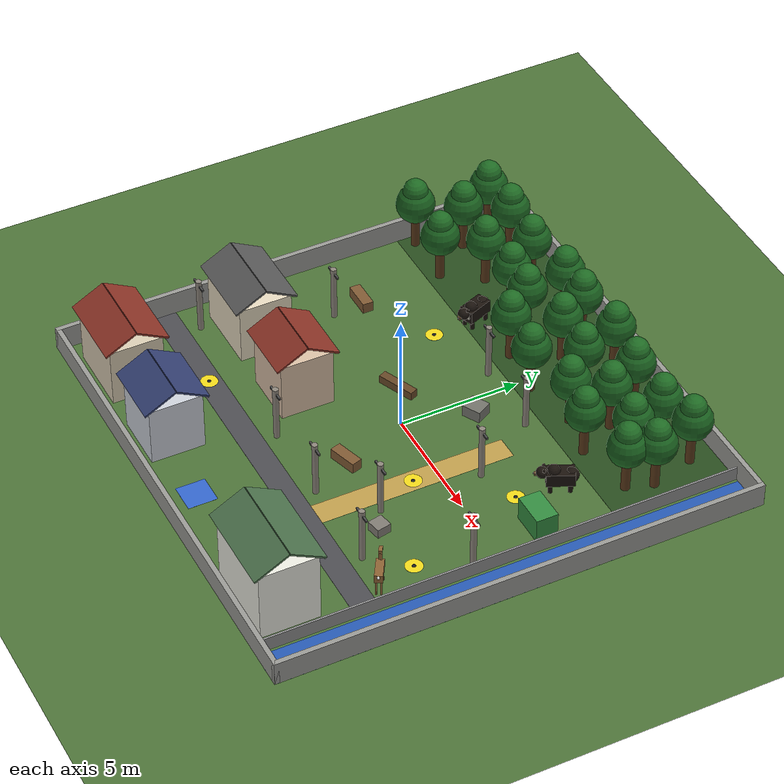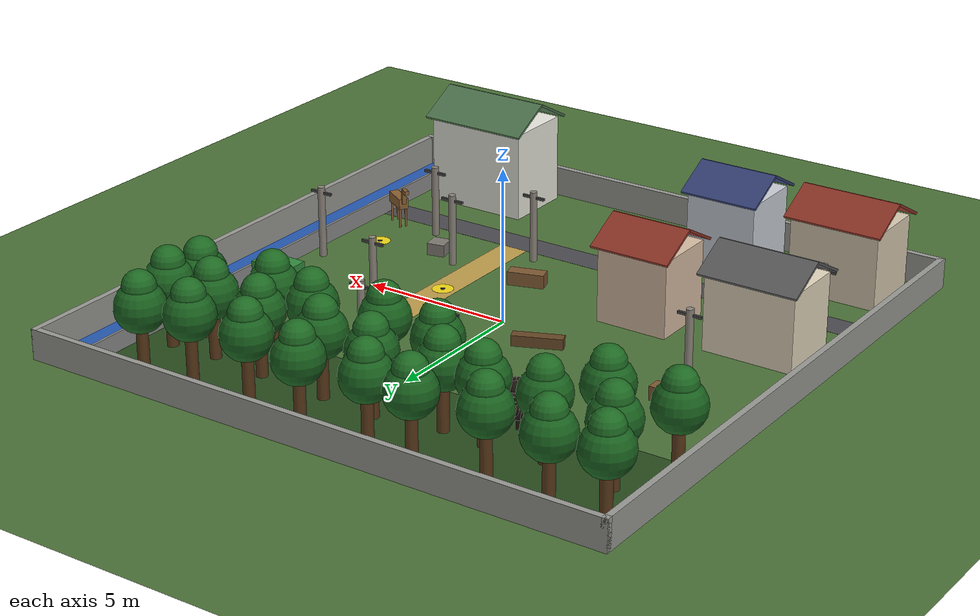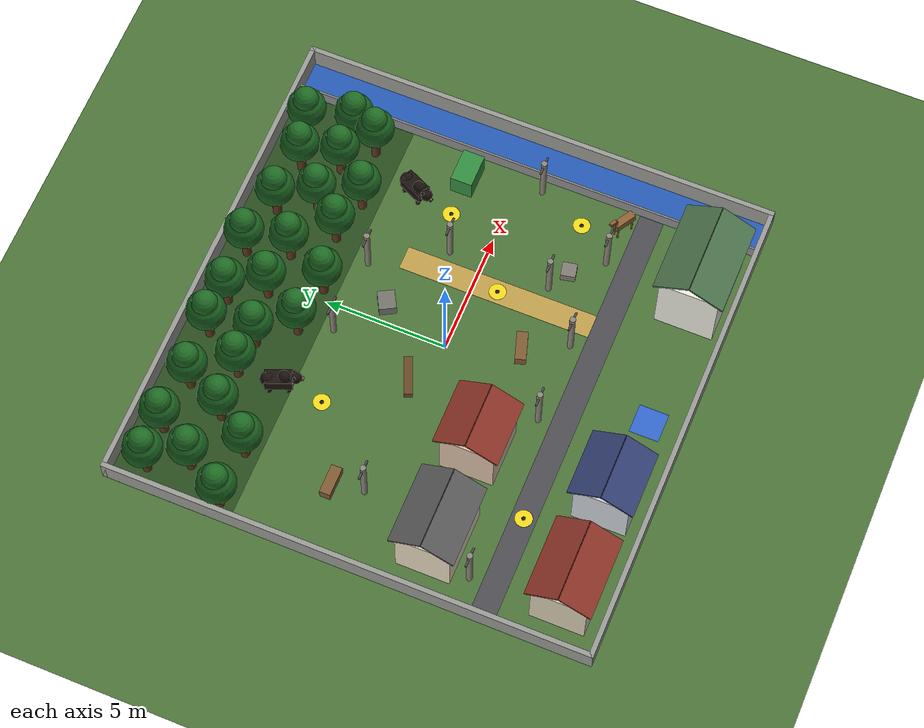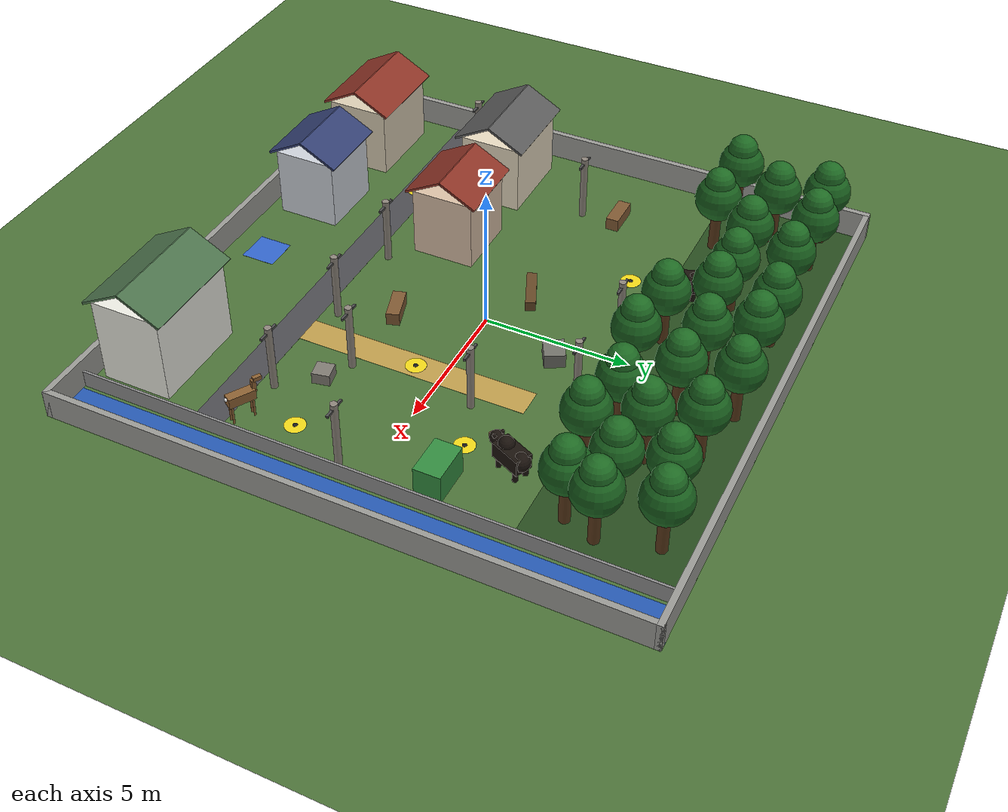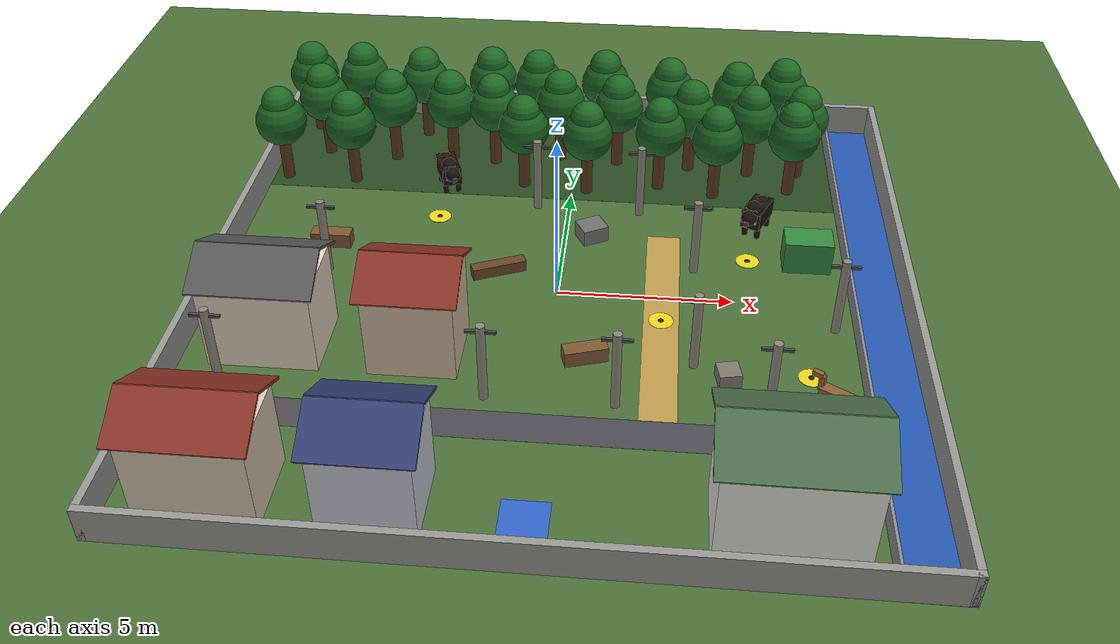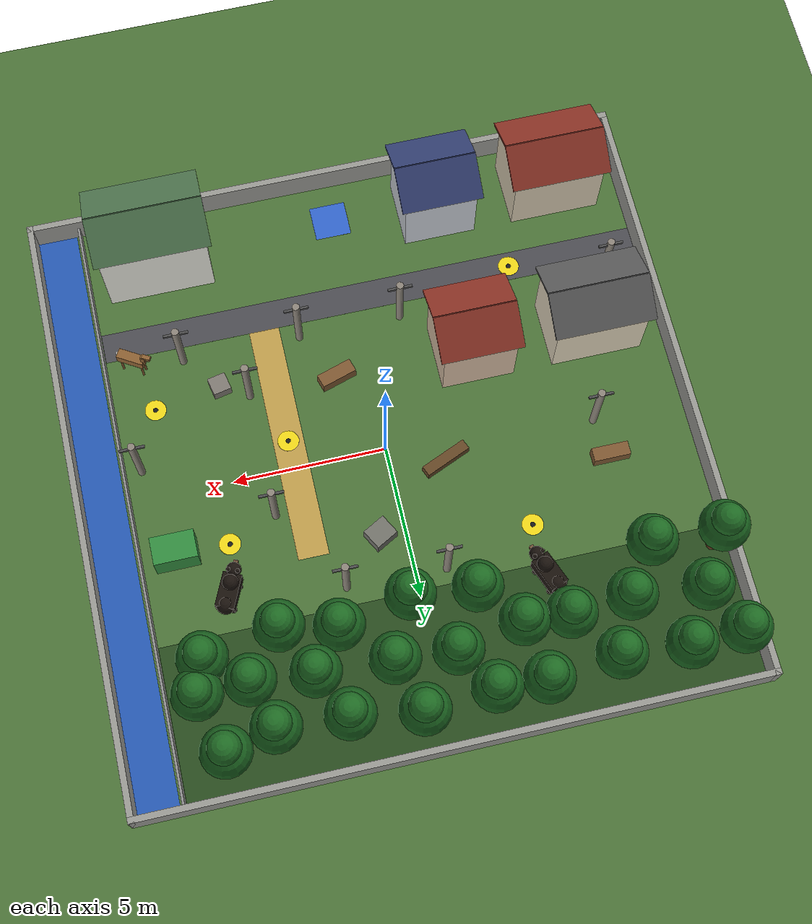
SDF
<?xml version="1.0"?>
<!-- KumaWatch Patrol world: generated by scripts/generate_world.py from world_layout.yaml. Do not edit by hand. -->
<sdf version="1.6">
  <world name="kumawatch_patrol">
    <gravity>0 0 -9.8</gravity>
    <physics type="ode">
      <max_step_size>0.001</max_step_size>
      <real_time_factor>1</real_time_factor>
      <real_time_update_rate>1000</real_time_update_rate>
    </physics>
    <scene>
      <ambient>0.6 0.6 0.6 1</ambient>
      <background>0.62 0.78 0.92 1</background>
      <shadows>false</shadows>
    </scene>
    <gui fullscreen="0">
      <camera name="user_camera">
        <pose>0 -19 17 0 0.78 1.5708</pose>
        <view_controller>orbit</view_controller>
      </camera>
    </gui>
    <plugin name="gazebo_ros_state" filename="libgazebo_ros_state.so">
      <ros>
        <namespace>/gazebo</namespace>
      </ros>
      <update_rate>1.0</update_rate>
    </plugin>
    <model name="ground_plane">
      <static>true</static>
      <link name="link">
        <collision name="collision">
          <geometry>
            <plane>
              <normal>0 0 1</normal>
              <size>60 60</size>
            </plane>
          </geometry>
          <surface>
            <friction>
              <ode>
                <mu>100</mu>
                <mu2>50</mu2>
              </ode>
            </friction>
          </surface>
        </collision>
        <visual name="visual">
          <cast_shadows>false</cast_shadows>
          <geometry>
            <plane>
              <normal>0 0 1</normal>
              <size>60 60</size>
            </plane>
          </geometry>
          <material>
            <ambient>0.30 0.45 0.22 1</ambient>
            <diffuse>0.30 0.45 0.22 1</diffuse>
          </material>
        </visual>
      </link>
    </model>
    <light name="sun" type="directional">
      <cast_shadows>false</cast_shadows>
      <pose>0 0 10 0 0 0</pose>
      <diffuse>0.9 0.9 0.85 1</diffuse>
      <specular>0.2 0.2 0.2 1</specular>
      <attenuation>
        <range>1000</range>
        <constant>0.9</constant>
        <linear>0.01</linear>
        <quadratic>0.001</quadratic>
      </attenuation>
      <direction>-0.4 0.3 -0.9</direction>
    </light>
    <model name="wall_north">
      <static>true</static>
      <pose>0.000 9.900 0.000 0.000 0.000 0.000</pose>
      <link name="link">
        <visual name="visual">
          <pose>0.000 0.000 0.500 0.000 0.000 0.000</pose>
          <geometry>
            <box>
              <size>20.000 0.200 1.000</size>
            </box>
          </geometry>
          <material>
            <ambient>0.600 0.600 0.580 1.00</ambient>
            <diffuse>0.600 0.600 0.580 1.00</diffuse>
            <specular>0.05 0.05 0.05 1</specular>
          </material>
        </visual>
        <collision name="collision">
          <pose>0.000 0.000 0.500 0.000 0.000 0.000</pose>
          <geometry>
            <box>
              <size>20.000 0.200 1.000</size>
            </box>
          </geometry>
        </collision>
      </link>
    </model>
    <model name="wall_south">
      <static>true</static>
      <pose>0.000 -9.900 0.000 0.000 0.000 0.000</pose>
      <link name="link">
        <visual name="visual">
          <pose>0.000 0.000 0.500 0.000 0.000 0.000</pose>
          <geometry>
            <box>
              <size>20.000 0.200 1.000</size>
            </box>
          </geometry>
          <material>
            <ambient>0.600 0.600 0.580 1.00</ambient>
            <diffuse>0.600 0.600 0.580 1.00</diffuse>
            <specular>0.05 0.05 0.05 1</specular>
          </material>
        </visual>
        <collision name="collision">
          <pose>0.000 0.000 0.500 0.000 0.000 0.000</pose>
          <geometry>
            <box>
              <size>20.000 0.200 1.000</size>
            </box>
          </geometry>
        </collision>
      </link>
    </model>
    <model name="wall_east">
      <static>true</static>
      <pose>9.900 0.000 0.000 0.000 0.000 0.000</pose>
      <link name="link">
        <visual name="visual">
          <pose>0.000 0.000 0.500 0.000 0.000 0.000</pose>
          <geometry>
            <box>
              <size>0.200 20.000 1.000</size>
            </box>
          </geometry>
          <material>
            <ambient>0.600 0.600 0.580 1.00</ambient>
            <diffuse>0.600 0.600 0.580 1.00</diffuse>
            <specular>0.05 0.05 0.05 1</specular>
          </material>
        </visual>
        <collision name="collision">
          <pose>0.000 0.000 0.500 0.000 0.000 0.000</pose>
          <geometry>
            <box>
              <size>0.200 20.000 1.000</size>
            </box>
          </geometry>
        </collision>
      </link>
    </model>
    <model name="wall_west">
      <static>true</static>
      <pose>-9.900 0.000 0.000 0.000 0.000 0.000</pose>
      <link name="link">
        <visual name="visual">
          <pose>0.000 0.000 0.500 0.000 0.000 0.000</pose>
          <geometry>
            <box>
              <size>0.200 20.000 1.000</size>
            </box>
          </geometry>
          <material>
            <ambient>0.600 0.600 0.580 1.00</ambient>
            <diffuse>0.600 0.600 0.580 1.00</diffuse>
            <specular>0.05 0.05 0.05 1</specular>
          </material>
        </visual>
        <collision name="collision">
          <pose>0.000 0.000 0.500 0.000 0.000 0.000</pose>
          <geometry>
            <box>
              <size>0.200 20.000 1.000</size>
            </box>
          </geometry>
        </collision>
      </link>
    </model>
    <model name="surface_forest_floor">
      <static>true</static>
      <pose>-0.850 7.400 0.000 0.000 0.000 0.000</pose>
      <link name="link">
        <visual name="visual">
          <pose>0.000 0.000 0.002 0.000 0.000 0.000</pose>
          <geometry>
            <box>
              <size>18.300 5.200 0.002</size>
            </box>
          </geometry>
          <material>
            <ambient>0.160 0.300 0.120 1.00</ambient>
            <diffuse>0.160 0.300 0.120 1.00</diffuse>
            <specular>0.05 0.05 0.05 1</specular>
          </material>
        </visual>
      </link>
    </model>
    <model name="surface_road">
      <static>true</static>
      <pose>-0.850 -5.500 0.000 0.000 0.000 0.000</pose>
      <link name="link">
        <visual name="visual">
          <pose>0.000 0.000 0.003 0.000 0.000 0.000</pose>
          <geometry>
            <box>
              <size>18.300 1.000 0.002</size>
            </box>
          </geometry>
          <material>
            <ambient>0.300 0.300 0.320 1.00</ambient>
            <diffuse>0.300 0.300 0.320 1.00</diffuse>
            <specular>0.05 0.05 0.05 1</specular>
          </material>
        </visual>
      </link>
    </model>
    <model name="surface_school_route">
      <static>true</static>
      <pose>3.000 -1.000 0.000 0.000 0.000 0.000</pose>
      <link name="link">
        <visual name="visual">
          <pose>0.000 0.000 0.004 0.000 0.000 0.000</pose>
          <geometry>
            <box>
              <size>1.000 8.000 0.002</size>
            </box>
          </geometry>
          <material>
            <ambient>0.750 0.620 0.300 1.00</ambient>
            <diffuse>0.750 0.620 0.300 1.00</diffuse>
            <specular>0.05 0.05 0.05 1</specular>
          </material>
        </visual>
      </link>
    </model>
    <model name="surface_river">
      <static>true</static>
      <pose>9.250 0.000 0.000 0.000 0.000 0.000</pose>
      <link name="link">
        <visual name="visual">
          <pose>0.000 0.000 0.005 0.000 0.000 0.000</pose>
          <geometry>
            <box>
              <size>1.500 20.000 0.002</size>
            </box>
          </geometry>
          <material>
            <ambient>0.150 0.350 0.700 1.00</ambient>
            <diffuse>0.150 0.350 0.700 1.00</diffuse>
            <specular>0.05 0.05 0.05 1</specular>
          </material>
        </visual>
      </link>
    </model>
    <model name="surface_base_pad">
      <static>true</static>
      <pose>0.000 -8.500 0.000 0.000 0.000 0.000</pose>
      <link name="link">
        <visual name="visual">
          <pose>0.000 0.000 0.006 0.000 0.000 0.000</pose>
          <geometry>
            <box>
              <size>1.200 1.200 0.002</size>
            </box>
          </geometry>
          <material>
            <ambient>0.200 0.400 0.800 1.00</ambient>
            <diffuse>0.200 0.400 0.800 1.00</diffuse>
            <specular>0.05 0.05 0.05 1</specular>
          </material>
        </visual>
      </link>
    </model>
    <model name="house_1">
      <static>true</static>
      <pose>-7.500 -8.200 0.000 0.000 0.000 0.000</pose>
      <link name="link">
        <visual name="walls">
          <pose>0.000 0.000 1.250 0.000 0.000 0.000</pose>
          <geometry>
            <box>
              <size>3.000 2.200 2.500</size>
            </box>
          </geometry>
          <material>
            <ambient>0.850 0.800 0.700 1.00</ambient>
            <diffuse>0.850 0.800 0.700 1.00</diffuse>
            <specular>0.05 0.05 0.05 1</specular>
          </material>
        </visual>
        <collision name="collision">
          <pose>0.000 0.000 1.250 0.000 0.000 0.000</pose>
          <geometry>
            <box>
              <size>3.000 2.200 2.500</size>
            </box>
          </geometry>
        </collision>
        <visual name="roof_0">
          <pose>0.000 0.650 2.855 -0.500 0.000 0.000</pose>
          <geometry>
            <box>
              <size>3.300 1.481 0.080</size>
            </box>
          </geometry>
          <material>
            <ambient>0.550 0.200 0.150 1.00</ambient>
            <diffuse>0.550 0.200 0.150 1.00</diffuse>
            <specular>0.05 0.05 0.05 1</specular>
          </material>
        </visual>
        <visual name="roof_1">
          <pose>0.000 -0.650 2.855 0.500 0.000 0.000</pose>
          <geometry>
            <box>
              <size>3.300 1.481 0.080</size>
            </box>
          </geometry>
          <material>
            <ambient>0.550 0.200 0.150 1.00</ambient>
            <diffuse>0.550 0.200 0.150 1.00</diffuse>
            <specular>0.05 0.05 0.05 1</specular>
          </material>
        </visual>
      </link>
    </model>
    <model name="house_2">
      <static>true</static>
      <pose>-3.500 -8.200 0.000 0.000 0.000 0.000</pose>
      <link name="link">
        <visual name="walls">
          <pose>0.000 0.000 1.250 0.000 0.000 0.000</pose>
          <geometry>
            <box>
              <size>2.400 2.200 2.500</size>
            </box>
          </geometry>
          <material>
            <ambient>0.800 0.820 0.850 1.00</ambient>
            <diffuse>0.800 0.820 0.850 1.00</diffuse>
            <specular>0.05 0.05 0.05 1</specular>
          </material>
        </visual>
        <collision name="collision">
          <pose>0.000 0.000 1.250 0.000 0.000 0.000</pose>
          <geometry>
            <box>
              <size>2.400 2.200 2.500</size>
            </box>
          </geometry>
        </collision>
        <visual name="roof_0">
          <pose>0.000 0.650 2.855 -0.500 0.000 0.000</pose>
          <geometry>
            <box>
              <size>2.700 1.481 0.080</size>
            </box>
          </geometry>
          <material>
            <ambient>0.200 0.250 0.450 1.00</ambient>
            <diffuse>0.200 0.250 0.450 1.00</diffuse>
            <specular>0.05 0.05 0.05 1</specular>
          </material>
        </visual>
        <visual name="roof_1">
          <pose>0.000 -0.650 2.855 0.500 0.000 0.000</pose>
          <geometry>
            <box>
              <size>2.700 1.481 0.080</size>
            </box>
          </geometry>
          <material>
            <ambient>0.200 0.250 0.450 1.00</ambient>
            <diffuse>0.200 0.250 0.450 1.00</diffuse>
            <specular>0.05 0.05 0.05 1</specular>
          </material>
        </visual>
      </link>
    </model>
    <model name="house_3">
      <static>true</static>
      <pose>-7.500 -2.800 0.000 0.000 0.000 0.000</pose>
      <link name="link">
        <visual name="walls">
          <pose>0.000 0.000 1.250 0.000 0.000 0.000</pose>
          <geometry>
            <box>
              <size>3.000 2.200 2.500</size>
            </box>
          </geometry>
          <material>
            <ambient>0.900 0.850 0.750 1.00</ambient>
            <diffuse>0.900 0.850 0.750 1.00</diffuse>
            <specular>0.05 0.05 0.05 1</specular>
          </material>
        </visual>
        <collision name="collision">
          <pose>0.000 0.000 1.250 0.000 0.000 0.000</pose>
          <geometry>
            <box>
              <size>3.000 2.200 2.500</size>
            </box>
          </geometry>
        </collision>
        <visual name="roof_0">
          <pose>0.000 0.650 2.855 -0.500 0.000 0.000</pose>
          <geometry>
            <box>
              <size>3.300 1.481 0.080</size>
            </box>
          </geometry>
          <material>
            <ambient>0.350 0.350 0.350 1.00</ambient>
            <diffuse>0.350 0.350 0.350 1.00</diffuse>
            <specular>0.05 0.05 0.05 1</specular>
          </material>
        </visual>
        <visual name="roof_1">
          <pose>0.000 -0.650 2.855 0.500 0.000 0.000</pose>
          <geometry>
            <box>
              <size>3.300 1.481 0.080</size>
            </box>
          </geometry>
          <material>
            <ambient>0.350 0.350 0.350 1.00</ambient>
            <diffuse>0.350 0.350 0.350 1.00</diffuse>
            <specular>0.05 0.05 0.05 1</specular>
          </material>
        </visual>
      </link>
    </model>
    <model name="house_4">
      <static>true</static>
      <pose>-3.500 -2.800 0.000 0.000 0.000 0.000</pose>
      <link name="link">
        <visual name="walls">
          <pose>0.000 0.000 1.250 0.000 0.000 0.000</pose>
          <geometry>
            <box>
              <size>2.400 2.200 2.500</size>
            </box>
          </geometry>
          <material>
            <ambient>0.850 0.750 0.650 1.00</ambient>
            <diffuse>0.850 0.750 0.650 1.00</diffuse>
            <specular>0.05 0.05 0.05 1</specular>
          </material>
        </visual>
        <collision name="collision">
          <pose>0.000 0.000 1.250 0.000 0.000 0.000</pose>
          <geometry>
            <box>
              <size>2.400 2.200 2.500</size>
            </box>
          </geometry>
        </collision>
        <visual name="roof_0">
          <pose>0.000 0.650 2.855 -0.500 0.000 0.000</pose>
          <geometry>
            <box>
              <size>2.700 1.481 0.080</size>
            </box>
          </geometry>
          <material>
            <ambient>0.550 0.200 0.150 1.00</ambient>
            <diffuse>0.550 0.200 0.150 1.00</diffuse>
            <specular>0.05 0.05 0.05 1</specular>
          </material>
        </visual>
        <visual name="roof_1">
          <pose>0.000 -0.650 2.855 0.500 0.000 0.000</pose>
          <geometry>
            <box>
              <size>2.700 1.481 0.080</size>
            </box>
          </geometry>
          <material>
            <ambient>0.550 0.200 0.150 1.00</ambient>
            <diffuse>0.550 0.200 0.150 1.00</diffuse>
            <specular>0.05 0.05 0.05 1</specular>
          </material>
        </visual>
      </link>
    </model>
    <model name="school">
      <static>true</static>
      <pose>6.000 -8.300 0.000 0.000 0.000 0.000</pose>
      <link name="link">
        <visual name="walls">
          <pose>0.000 0.000 1.500 0.000 0.000 0.000</pose>
          <geometry>
            <box>
              <size>3.500 2.400 3.000</size>
            </box>
          </geometry>
          <material>
            <ambient>0.920 0.920 0.880 1.00</ambient>
            <diffuse>0.920 0.920 0.880 1.00</diffuse>
            <specular>0.05 0.05 0.05 1</specular>
          </material>
        </visual>
        <collision name="collision">
          <pose>0.000 0.000 1.500 0.000 0.000 0.000</pose>
          <geometry>
            <box>
              <size>3.500 2.400 3.000</size>
            </box>
          </geometry>
        </collision>
        <visual name="roof_0">
          <pose>0.000 0.700 3.382 -0.500 0.000 0.000</pose>
          <geometry>
            <box>
              <size>3.800 1.595 0.080</size>
            </box>
          </geometry>
          <material>
            <ambient>0.300 0.450 0.300 1.00</ambient>
            <diffuse>0.300 0.450 0.300 1.00</diffuse>
            <specular>0.05 0.05 0.05 1</specular>
          </material>
        </visual>
        <visual name="roof_1">
          <pose>0.000 -0.700 3.382 0.500 0.000 0.000</pose>
          <geometry>
            <box>
              <size>3.800 1.595 0.080</size>
            </box>
          </geometry>
          <material>
            <ambient>0.300 0.450 0.300 1.00</ambient>
            <diffuse>0.300 0.450 0.300 1.00</diffuse>
            <specular>0.05 0.05 0.05 1</specular>
          </material>
        </visual>
      </link>
    </model>
    <model name="tree_00">
      <static>true</static>
      <pose>-9.340 5.390 0.000 0.000 0.000 0.000</pose>
      <link name="link">
        <visual name="trunk">
          <pose>0.000 0.000 0.800 0.000 0.000 0.000</pose>
          <geometry>
            <cylinder>
              <radius>0.180</radius>
              <length>1.600</length>
            </cylinder>
          </geometry>
          <material>
            <ambient>0.350 0.220 0.100 1.00</ambient>
            <diffuse>0.350 0.220 0.100 1.00</diffuse>
            <specular>0.05 0.05 0.05 1</specular>
          </material>
        </visual>
        <collision name="collision">
          <pose>0.000 0.000 0.800 0.000 0.000 0.000</pose>
          <geometry>
            <cylinder>
              <radius>0.180</radius>
              <length>1.600</length>
            </cylinder>
          </geometry>
        </collision>
        <visual name="canopy">
          <pose>0.000 0.000 2.080 0.000 0.000 0.000</pose>
          <geometry>
            <sphere>
              <radius>0.800</radius>
            </sphere>
          </geometry>
          <material>
            <ambient>0.100 0.380 0.120 1.00</ambient>
            <diffuse>0.100 0.380 0.120 1.00</diffuse>
            <specular>0.05 0.05 0.05 1</specular>
          </material>
        </visual>
        <visual name="canopy_top">
          <pose>0.000 0.000 2.720 0.000 0.000 0.000</pose>
          <geometry>
            <sphere>
              <radius>0.520</radius>
            </sphere>
          </geometry>
          <material>
            <ambient>0.120 0.420 0.140 1.00</ambient>
            <diffuse>0.120 0.420 0.140 1.00</diffuse>
            <specular>0.05 0.05 0.05 1</specular>
          </material>
        </visual>
      </link>
    </model>
    <model name="tree_01">
      <static>true</static>
      <pose>-7.080 5.340 0.000 0.000 0.000 0.000</pose>
      <link name="link">
        <visual name="trunk">
          <pose>0.000 0.000 0.800 0.000 0.000 0.000</pose>
          <geometry>
            <cylinder>
              <radius>0.180</radius>
              <length>1.600</length>
            </cylinder>
          </geometry>
          <material>
            <ambient>0.350 0.220 0.100 1.00</ambient>
            <diffuse>0.350 0.220 0.100 1.00</diffuse>
            <specular>0.05 0.05 0.05 1</specular>
          </material>
        </visual>
        <collision name="collision">
          <pose>0.000 0.000 0.800 0.000 0.000 0.000</pose>
          <geometry>
            <cylinder>
              <radius>0.180</radius>
              <length>1.600</length>
            </cylinder>
          </geometry>
        </collision>
        <visual name="canopy">
          <pose>0.000 0.000 2.080 0.000 0.000 0.000</pose>
          <geometry>
            <sphere>
              <radius>0.800</radius>
            </sphere>
          </geometry>
          <material>
            <ambient>0.100 0.380 0.120 1.00</ambient>
            <diffuse>0.100 0.380 0.120 1.00</diffuse>
            <specular>0.05 0.05 0.05 1</specular>
          </material>
        </visual>
        <visual name="canopy_top">
          <pose>0.000 0.000 2.720 0.000 0.000 0.000</pose>
          <geometry>
            <sphere>
              <radius>0.520</radius>
            </sphere>
          </geometry>
          <material>
            <ambient>0.120 0.420 0.140 1.00</ambient>
            <diffuse>0.120 0.420 0.140 1.00</diffuse>
            <specular>0.05 0.05 0.05 1</specular>
          </material>
        </visual>
      </link>
    </model>
    <model name="tree_02">
      <static>true</static>
      <pose>-1.570 5.560 0.000 0.000 0.000 0.000</pose>
      <link name="link">
        <visual name="trunk">
          <pose>0.000 0.000 0.800 0.000 0.000 0.000</pose>
          <geometry>
            <cylinder>
              <radius>0.180</radius>
              <length>1.600</length>
            </cylinder>
          </geometry>
          <material>
            <ambient>0.350 0.220 0.100 1.00</ambient>
            <diffuse>0.350 0.220 0.100 1.00</diffuse>
            <specular>0.05 0.05 0.05 1</specular>
          </material>
        </visual>
        <collision name="collision">
          <pose>0.000 0.000 0.800 0.000 0.000 0.000</pose>
          <geometry>
            <cylinder>
              <radius>0.180</radius>
              <length>1.600</length>
            </cylinder>
          </geometry>
        </collision>
        <visual name="canopy">
          <pose>0.000 0.000 2.080 0.000 0.000 0.000</pose>
          <geometry>
            <sphere>
              <radius>0.800</radius>
            </sphere>
          </geometry>
          <material>
            <ambient>0.100 0.380 0.120 1.00</ambient>
            <diffuse>0.100 0.380 0.120 1.00</diffuse>
            <specular>0.05 0.05 0.05 1</specular>
          </material>
        </visual>
        <visual name="canopy_top">
          <pose>0.000 0.000 2.720 0.000 0.000 0.000</pose>
          <geometry>
            <sphere>
              <radius>0.520</radius>
            </sphere>
          </geometry>
          <material>
            <ambient>0.120 0.420 0.140 1.00</ambient>
            <diffuse>0.120 0.420 0.140 1.00</diffuse>
            <specular>0.05 0.05 0.05 1</specular>
          </material>
        </visual>
      </link>
    </model>
    <model name="tree_03">
      <static>true</static>
      <pose>0.460 5.350 0.000 0.000 0.000 0.000</pose>
      <link name="link">
        <visual name="trunk">
          <pose>0.000 0.000 0.800 0.000 0.000 0.000</pose>
          <geometry>
            <cylinder>
              <radius>0.180</radius>
              <length>1.600</length>
            </cylinder>
          </geometry>
          <material>
            <ambient>0.350 0.220 0.100 1.00</ambient>
            <diffuse>0.350 0.220 0.100 1.00</diffuse>
            <specular>0.05 0.05 0.05 1</specular>
          </material>
        </visual>
        <collision name="collision">
          <pose>0.000 0.000 0.800 0.000 0.000 0.000</pose>
          <geometry>
            <cylinder>
              <radius>0.180</radius>
              <length>1.600</length>
            </cylinder>
          </geometry>
        </collision>
        <visual name="canopy">
          <pose>0.000 0.000 2.080 0.000 0.000 0.000</pose>
          <geometry>
            <sphere>
              <radius>0.800</radius>
            </sphere>
          </geometry>
          <material>
            <ambient>0.100 0.380 0.120 1.00</ambient>
            <diffuse>0.100 0.380 0.120 1.00</diffuse>
            <specular>0.05 0.05 0.05 1</specular>
          </material>
        </visual>
        <visual name="canopy_top">
          <pose>0.000 0.000 2.720 0.000 0.000 0.000</pose>
          <geometry>
            <sphere>
              <radius>0.520</radius>
            </sphere>
          </geometry>
          <material>
            <ambient>0.120 0.420 0.140 1.00</ambient>
            <diffuse>0.120 0.420 0.140 1.00</diffuse>
            <specular>0.05 0.05 0.05 1</specular>
          </material>
        </visual>
      </link>
    </model>
    <model name="tree_04">
      <static>true</static>
      <pose>2.740 5.800 0.000 0.000 0.000 0.000</pose>
      <link name="link">
        <visual name="trunk">
          <pose>0.000 0.000 0.800 0.000 0.000 0.000</pose>
          <geometry>
            <cylinder>
              <radius>0.180</radius>
              <length>1.600</length>
            </cylinder>
          </geometry>
          <material>
            <ambient>0.350 0.220 0.100 1.00</ambient>
            <diffuse>0.350 0.220 0.100 1.00</diffuse>
            <specular>0.05 0.05 0.05 1</specular>
          </material>
        </visual>
        <collision name="collision">
          <pose>0.000 0.000 0.800 0.000 0.000 0.000</pose>
          <geometry>
            <cylinder>
              <radius>0.180</radius>
              <length>1.600</length>
            </cylinder>
          </geometry>
        </collision>
        <visual name="canopy">
          <pose>0.000 0.000 2.080 0.000 0.000 0.000</pose>
          <geometry>
            <sphere>
              <radius>0.800</radius>
            </sphere>
          </geometry>
          <material>
            <ambient>0.100 0.380 0.120 1.00</ambient>
            <diffuse>0.100 0.380 0.120 1.00</diffuse>
            <specular>0.05 0.05 0.05 1</specular>
          </material>
        </visual>
        <visual name="canopy_top">
          <pose>0.000 0.000 2.720 0.000 0.000 0.000</pose>
          <geometry>
            <sphere>
              <radius>0.520</radius>
            </sphere>
          </geometry>
          <material>
            <ambient>0.120 0.420 0.140 1.00</ambient>
            <diffuse>0.120 0.420 0.140 1.00</diffuse>
            <specular>0.05 0.05 0.05 1</specular>
          </material>
        </visual>
      </link>
    </model>
    <model name="tree_05">
      <static>true</static>
      <pose>4.500 5.430 0.000 0.000 0.000 0.000</pose>
      <link name="link">
        <visual name="trunk">
          <pose>0.000 0.000 0.800 0.000 0.000 0.000</pose>
          <geometry>
            <cylinder>
              <radius>0.180</radius>
              <length>1.600</length>
            </cylinder>
          </geometry>
          <material>
            <ambient>0.350 0.220 0.100 1.00</ambient>
            <diffuse>0.350 0.220 0.100 1.00</diffuse>
            <specular>0.05 0.05 0.05 1</specular>
          </material>
        </visual>
        <collision name="collision">
          <pose>0.000 0.000 0.800 0.000 0.000 0.000</pose>
          <geometry>
            <cylinder>
              <radius>0.180</radius>
              <length>1.600</length>
            </cylinder>
          </geometry>
        </collision>
        <visual name="canopy">
          <pose>0.000 0.000 2.080 0.000 0.000 0.000</pose>
          <geometry>
            <sphere>
              <radius>0.800</radius>
            </sphere>
          </geometry>
          <material>
            <ambient>0.100 0.380 0.120 1.00</ambient>
            <diffuse>0.100 0.380 0.120 1.00</diffuse>
            <specular>0.05 0.05 0.05 1</specular>
          </material>
        </visual>
        <visual name="canopy_top">
          <pose>0.000 0.000 2.720 0.000 0.000 0.000</pose>
          <geometry>
            <sphere>
              <radius>0.520</radius>
            </sphere>
          </geometry>
          <material>
            <ambient>0.120 0.420 0.140 1.00</ambient>
            <diffuse>0.120 0.420 0.140 1.00</diffuse>
            <specular>0.05 0.05 0.05 1</specular>
          </material>
        </visual>
      </link>
    </model>
    <model name="tree_06">
      <static>true</static>
      <pose>6.900 5.870 0.000 0.000 0.000 0.000</pose>
      <link name="link">
        <visual name="trunk">
          <pose>0.000 0.000 0.800 0.000 0.000 0.000</pose>
          <geometry>
            <cylinder>
              <radius>0.180</radius>
              <length>1.600</length>
            </cylinder>
          </geometry>
          <material>
            <ambient>0.350 0.220 0.100 1.00</ambient>
            <diffuse>0.350 0.220 0.100 1.00</diffuse>
            <specular>0.05 0.05 0.05 1</specular>
          </material>
        </visual>
        <collision name="collision">
          <pose>0.000 0.000 0.800 0.000 0.000 0.000</pose>
          <geometry>
            <cylinder>
              <radius>0.180</radius>
              <length>1.600</length>
            </cylinder>
          </geometry>
        </collision>
        <visual name="canopy">
          <pose>0.000 0.000 2.080 0.000 0.000 0.000</pose>
          <geometry>
            <sphere>
              <radius>0.800</radius>
            </sphere>
          </geometry>
          <material>
            <ambient>0.100 0.380 0.120 1.00</ambient>
            <diffuse>0.100 0.380 0.120 1.00</diffuse>
            <specular>0.05 0.05 0.05 1</specular>
          </material>
        </visual>
        <visual name="canopy_top">
          <pose>0.000 0.000 2.720 0.000 0.000 0.000</pose>
          <geometry>
            <sphere>
              <radius>0.520</radius>
            </sphere>
          </geometry>
          <material>
            <ambient>0.120 0.420 0.140 1.00</ambient>
            <diffuse>0.120 0.420 0.140 1.00</diffuse>
            <specular>0.05 0.05 0.05 1</specular>
          </material>
        </visual>
      </link>
    </model>
    <model name="tree_07">
      <static>true</static>
      <pose>-8.340 7.040 0.000 0.000 0.000 0.000</pose>
      <link name="link">
        <visual name="trunk">
          <pose>0.000 0.000 0.800 0.000 0.000 0.000</pose>
          <geometry>
            <cylinder>
              <radius>0.180</radius>
              <length>1.600</length>
            </cylinder>
          </geometry>
          <material>
            <ambient>0.350 0.220 0.100 1.00</ambient>
            <diffuse>0.350 0.220 0.100 1.00</diffuse>
            <specular>0.05 0.05 0.05 1</specular>
          </material>
        </visual>
        <collision name="collision">
          <pose>0.000 0.000 0.800 0.000 0.000 0.000</pose>
          <geometry>
            <cylinder>
              <radius>0.180</radius>
              <length>1.600</length>
            </cylinder>
          </geometry>
        </collision>
        <visual name="canopy">
          <pose>0.000 0.000 2.080 0.000 0.000 0.000</pose>
          <geometry>
            <sphere>
              <radius>0.800</radius>
            </sphere>
          </geometry>
          <material>
            <ambient>0.100 0.380 0.120 1.00</ambient>
            <diffuse>0.100 0.380 0.120 1.00</diffuse>
            <specular>0.05 0.05 0.05 1</specular>
          </material>
        </visual>
        <visual name="canopy_top">
          <pose>0.000 0.000 2.720 0.000 0.000 0.000</pose>
          <geometry>
            <sphere>
              <radius>0.520</radius>
            </sphere>
          </geometry>
          <material>
            <ambient>0.120 0.420 0.140 1.00</ambient>
            <diffuse>0.120 0.420 0.140 1.00</diffuse>
            <specular>0.05 0.05 0.05 1</specular>
          </material>
        </visual>
      </link>
    </model>
    <model name="tree_08">
      <static>true</static>
      <pose>-6.020 6.830 0.000 0.000 0.000 0.000</pose>
      <link name="link">
        <visual name="trunk">
          <pose>0.000 0.000 0.800 0.000 0.000 0.000</pose>
          <geometry>
            <cylinder>
              <radius>0.180</radius>
              <length>1.600</length>
            </cylinder>
          </geometry>
          <material>
            <ambient>0.350 0.220 0.100 1.00</ambient>
            <diffuse>0.350 0.220 0.100 1.00</diffuse>
            <specular>0.05 0.05 0.05 1</specular>
          </material>
        </visual>
        <collision name="collision">
          <pose>0.000 0.000 0.800 0.000 0.000 0.000</pose>
          <geometry>
            <cylinder>
              <radius>0.180</radius>
              <length>1.600</length>
            </cylinder>
          </geometry>
        </collision>
        <visual name="canopy">
          <pose>0.000 0.000 2.080 0.000 0.000 0.000</pose>
          <geometry>
            <sphere>
              <radius>0.800</radius>
            </sphere>
          </geometry>
          <material>
            <ambient>0.100 0.380 0.120 1.00</ambient>
            <diffuse>0.100 0.380 0.120 1.00</diffuse>
            <specular>0.05 0.05 0.05 1</specular>
          </material>
        </visual>
        <visual name="canopy_top">
          <pose>0.000 0.000 2.720 0.000 0.000 0.000</pose>
          <geometry>
            <sphere>
              <radius>0.520</radius>
            </sphere>
          </geometry>
          <material>
            <ambient>0.120 0.420 0.140 1.00</ambient>
            <diffuse>0.120 0.420 0.140 1.00</diffuse>
            <specular>0.05 0.05 0.05 1</specular>
          </material>
        </visual>
      </link>
    </model>
    <model name="tree_09">
      <static>true</static>
      <pose>-4.110 6.970 0.000 0.000 0.000 0.000</pose>
      <link name="link">
        <visual name="trunk">
          <pose>0.000 0.000 0.800 0.000 0.000 0.000</pose>
          <geometry>
            <cylinder>
              <radius>0.180</radius>
              <length>1.600</length>
            </cylinder>
          </geometry>
          <material>
            <ambient>0.350 0.220 0.100 1.00</ambient>
            <diffuse>0.350 0.220 0.100 1.00</diffuse>
            <specular>0.05 0.05 0.05 1</specular>
          </material>
        </visual>
        <collision name="collision">
          <pose>0.000 0.000 0.800 0.000 0.000 0.000</pose>
          <geometry>
            <cylinder>
              <radius>0.180</radius>
              <length>1.600</length>
            </cylinder>
          </geometry>
        </collision>
        <visual name="canopy">
          <pose>0.000 0.000 2.080 0.000 0.000 0.000</pose>
          <geometry>
            <sphere>
              <radius>0.800</radius>
            </sphere>
          </geometry>
          <material>
            <ambient>0.100 0.380 0.120 1.00</ambient>
            <diffuse>0.100 0.380 0.120 1.00</diffuse>
            <specular>0.05 0.05 0.05 1</specular>
          </material>
        </visual>
        <visual name="canopy_top">
          <pose>0.000 0.000 2.720 0.000 0.000 0.000</pose>
          <geometry>
            <sphere>
              <radius>0.520</radius>
            </sphere>
          </geometry>
          <material>
            <ambient>0.120 0.420 0.140 1.00</ambient>
            <diffuse>0.120 0.420 0.140 1.00</diffuse>
            <specular>0.05 0.05 0.05 1</specular>
          </material>
        </visual>
      </link>
    </model>
    <model name="tree_10">
      <static>true</static>
      <pose>-2.680 6.870 0.000 0.000 0.000 0.000</pose>
      <link name="link">
        <visual name="trunk">
          <pose>0.000 0.000 0.800 0.000 0.000 0.000</pose>
          <geometry>
            <cylinder>
              <radius>0.180</radius>
              <length>1.600</length>
            </cylinder>
          </geometry>
          <material>
            <ambient>0.350 0.220 0.100 1.00</ambient>
            <diffuse>0.350 0.220 0.100 1.00</diffuse>
            <specular>0.05 0.05 0.05 1</specular>
          </material>
        </visual>
        <collision name="collision">
          <pose>0.000 0.000 0.800 0.000 0.000 0.000</pose>
          <geometry>
            <cylinder>
              <radius>0.180</radius>
              <length>1.600</length>
            </cylinder>
          </geometry>
        </collision>
        <visual name="canopy">
          <pose>0.000 0.000 2.080 0.000 0.000 0.000</pose>
          <geometry>
            <sphere>
              <radius>0.800</radius>
            </sphere>
          </geometry>
          <material>
            <ambient>0.100 0.380 0.120 1.00</ambient>
            <diffuse>0.100 0.380 0.120 1.00</diffuse>
            <specular>0.05 0.05 0.05 1</specular>
          </material>
        </visual>
        <visual name="canopy_top">
          <pose>0.000 0.000 2.720 0.000 0.000 0.000</pose>
          <geometry>
            <sphere>
              <radius>0.520</radius>
            </sphere>
          </geometry>
          <material>
            <ambient>0.120 0.420 0.140 1.00</ambient>
            <diffuse>0.120 0.420 0.140 1.00</diffuse>
            <specular>0.05 0.05 0.05 1</specular>
          </material>
        </visual>
      </link>
    </model>
    <model name="tree_11">
      <static>true</static>
      <pose>-0.550 7.290 0.000 0.000 0.000 0.000</pose>
      <link name="link">
        <visual name="trunk">
          <pose>0.000 0.000 0.800 0.000 0.000 0.000</pose>
          <geometry>
            <cylinder>
              <radius>0.180</radius>
              <length>1.600</length>
            </cylinder>
          </geometry>
          <material>
            <ambient>0.350 0.220 0.100 1.00</ambient>
            <diffuse>0.350 0.220 0.100 1.00</diffuse>
            <specular>0.05 0.05 0.05 1</specular>
          </material>
        </visual>
        <collision name="collision">
          <pose>0.000 0.000 0.800 0.000 0.000 0.000</pose>
          <geometry>
            <cylinder>
              <radius>0.180</radius>
              <length>1.600</length>
            </cylinder>
          </geometry>
        </collision>
        <visual name="canopy">
          <pose>0.000 0.000 2.080 0.000 0.000 0.000</pose>
          <geometry>
            <sphere>
              <radius>0.800</radius>
            </sphere>
          </geometry>
          <material>
            <ambient>0.100 0.380 0.120 1.00</ambient>
            <diffuse>0.100 0.380 0.120 1.00</diffuse>
            <specular>0.05 0.05 0.05 1</specular>
          </material>
        </visual>
        <visual name="canopy_top">
          <pose>0.000 0.000 2.720 0.000 0.000 0.000</pose>
          <geometry>
            <sphere>
              <radius>0.520</radius>
            </sphere>
          </geometry>
          <material>
            <ambient>0.120 0.420 0.140 1.00</ambient>
            <diffuse>0.120 0.420 0.140 1.00</diffuse>
            <specular>0.05 0.05 0.05 1</specular>
          </material>
        </visual>
      </link>
    </model>
    <model name="tree_12">
      <static>true</static>
      <pose>1.340 7.150 0.000 0.000 0.000 0.000</pose>
      <link name="link">
        <visual name="trunk">
          <pose>0.000 0.000 0.800 0.000 0.000 0.000</pose>
          <geometry>
            <cylinder>
              <radius>0.180</radius>
              <length>1.600</length>
            </cylinder>
          </geometry>
          <material>
            <ambient>0.350 0.220 0.100 1.00</ambient>
            <diffuse>0.350 0.220 0.100 1.00</diffuse>
            <specular>0.05 0.05 0.05 1</specular>
          </material>
        </visual>
        <collision name="collision">
          <pose>0.000 0.000 0.800 0.000 0.000 0.000</pose>
          <geometry>
            <cylinder>
              <radius>0.180</radius>
              <length>1.600</length>
            </cylinder>
          </geometry>
        </collision>
        <visual name="canopy">
          <pose>0.000 0.000 2.080 0.000 0.000 0.000</pose>
          <geometry>
            <sphere>
              <radius>0.800</radius>
            </sphere>
          </geometry>
          <material>
            <ambient>0.100 0.380 0.120 1.00</ambient>
            <diffuse>0.100 0.380 0.120 1.00</diffuse>
            <specular>0.05 0.05 0.05 1</specular>
          </material>
        </visual>
        <visual name="canopy_top">
          <pose>0.000 0.000 2.720 0.000 0.000 0.000</pose>
          <geometry>
            <sphere>
              <radius>0.520</radius>
            </sphere>
          </geometry>
          <material>
            <ambient>0.120 0.420 0.140 1.00</ambient>
            <diffuse>0.120 0.420 0.140 1.00</diffuse>
            <specular>0.05 0.05 0.05 1</specular>
          </material>
        </visual>
      </link>
    </model>
    <model name="tree_13">
      <static>true</static>
      <pose>3.710 7.020 0.000 0.000 0.000 0.000</pose>
      <link name="link">
        <visual name="trunk">
          <pose>0.000 0.000 0.800 0.000 0.000 0.000</pose>
          <geometry>
            <cylinder>
              <radius>0.180</radius>
              <length>1.600</length>
            </cylinder>
          </geometry>
          <material>
            <ambient>0.350 0.220 0.100 1.00</ambient>
            <diffuse>0.350 0.220 0.100 1.00</diffuse>
            <specular>0.05 0.05 0.05 1</specular>
          </material>
        </visual>
        <collision name="collision">
          <pose>0.000 0.000 0.800 0.000 0.000 0.000</pose>
          <geometry>
            <cylinder>
              <radius>0.180</radius>
              <length>1.600</length>
            </cylinder>
          </geometry>
        </collision>
        <visual name="canopy">
          <pose>0.000 0.000 2.080 0.000 0.000 0.000</pose>
          <geometry>
            <sphere>
              <radius>0.800</radius>
            </sphere>
          </geometry>
          <material>
            <ambient>0.100 0.380 0.120 1.00</ambient>
            <diffuse>0.100 0.380 0.120 1.00</diffuse>
            <specular>0.05 0.05 0.05 1</specular>
          </material>
        </visual>
        <visual name="canopy_top">
          <pose>0.000 0.000 2.720 0.000 0.000 0.000</pose>
          <geometry>
            <sphere>
              <radius>0.520</radius>
            </sphere>
          </geometry>
          <material>
            <ambient>0.120 0.420 0.140 1.00</ambient>
            <diffuse>0.120 0.420 0.140 1.00</diffuse>
            <specular>0.05 0.05 0.05 1</specular>
          </material>
        </visual>
      </link>
    </model>
    <model name="tree_14">
      <static>true</static>
      <pose>5.640 6.840 0.000 0.000 0.000 0.000</pose>
      <link name="link">
        <visual name="trunk">
          <pose>0.000 0.000 0.800 0.000 0.000 0.000</pose>
          <geometry>
            <cylinder>
              <radius>0.180</radius>
              <length>1.600</length>
            </cylinder>
          </geometry>
          <material>
            <ambient>0.350 0.220 0.100 1.00</ambient>
            <diffuse>0.350 0.220 0.100 1.00</diffuse>
            <specular>0.05 0.05 0.05 1</specular>
          </material>
        </visual>
        <collision name="collision">
          <pose>0.000 0.000 0.800 0.000 0.000 0.000</pose>
          <geometry>
            <cylinder>
              <radius>0.180</radius>
              <length>1.600</length>
            </cylinder>
          </geometry>
        </collision>
        <visual name="canopy">
          <pose>0.000 0.000 2.080 0.000 0.000 0.000</pose>
          <geometry>
            <sphere>
              <radius>0.800</radius>
            </sphere>
          </geometry>
          <material>
            <ambient>0.100 0.380 0.120 1.00</ambient>
            <diffuse>0.100 0.380 0.120 1.00</diffuse>
            <specular>0.05 0.05 0.05 1</specular>
          </material>
        </visual>
        <visual name="canopy_top">
          <pose>0.000 0.000 2.720 0.000 0.000 0.000</pose>
          <geometry>
            <sphere>
              <radius>0.520</radius>
            </sphere>
          </geometry>
          <material>
            <ambient>0.120 0.420 0.140 1.00</ambient>
            <diffuse>0.120 0.420 0.140 1.00</diffuse>
            <specular>0.05 0.05 0.05 1</specular>
          </material>
        </visual>
      </link>
    </model>
    <model name="tree_15">
      <static>true</static>
      <pose>7.250 6.920 0.000 0.000 0.000 0.000</pose>
      <link name="link">
        <visual name="trunk">
          <pose>0.000 0.000 0.800 0.000 0.000 0.000</pose>
          <geometry>
            <cylinder>
              <radius>0.180</radius>
              <length>1.600</length>
            </cylinder>
          </geometry>
          <material>
            <ambient>0.350 0.220 0.100 1.00</ambient>
            <diffuse>0.350 0.220 0.100 1.00</diffuse>
            <specular>0.05 0.05 0.05 1</specular>
          </material>
        </visual>
        <collision name="collision">
          <pose>0.000 0.000 0.800 0.000 0.000 0.000</pose>
          <geometry>
            <cylinder>
              <radius>0.180</radius>
              <length>1.600</length>
            </cylinder>
          </geometry>
        </collision>
        <visual name="canopy">
          <pose>0.000 0.000 2.080 0.000 0.000 0.000</pose>
          <geometry>
            <sphere>
              <radius>0.800</radius>
            </sphere>
          </geometry>
          <material>
            <ambient>0.100 0.380 0.120 1.00</ambient>
            <diffuse>0.100 0.380 0.120 1.00</diffuse>
            <specular>0.05 0.05 0.05 1</specular>
          </material>
        </visual>
        <visual name="canopy_top">
          <pose>0.000 0.000 2.720 0.000 0.000 0.000</pose>
          <geometry>
            <sphere>
              <radius>0.520</radius>
            </sphere>
          </geometry>
          <material>
            <ambient>0.120 0.420 0.140 1.00</ambient>
            <diffuse>0.120 0.420 0.140 1.00</diffuse>
            <specular>0.05 0.05 0.05 1</specular>
          </material>
        </visual>
      </link>
    </model>
    <model name="tree_16">
      <static>true</static>
      <pose>-9.060 8.560 0.000 0.000 0.000 0.000</pose>
      <link name="link">
        <visual name="trunk">
          <pose>0.000 0.000 0.800 0.000 0.000 0.000</pose>
          <geometry>
            <cylinder>
              <radius>0.180</radius>
              <length>1.600</length>
            </cylinder>
          </geometry>
          <material>
            <ambient>0.350 0.220 0.100 1.00</ambient>
            <diffuse>0.350 0.220 0.100 1.00</diffuse>
            <specular>0.05 0.05 0.05 1</specular>
          </material>
        </visual>
        <collision name="collision">
          <pose>0.000 0.000 0.800 0.000 0.000 0.000</pose>
          <geometry>
            <cylinder>
              <radius>0.180</radius>
              <length>1.600</length>
            </cylinder>
          </geometry>
        </collision>
        <visual name="canopy">
          <pose>0.000 0.000 2.080 0.000 0.000 0.000</pose>
          <geometry>
            <sphere>
              <radius>0.800</radius>
            </sphere>
          </geometry>
          <material>
            <ambient>0.100 0.380 0.120 1.00</ambient>
            <diffuse>0.100 0.380 0.120 1.00</diffuse>
            <specular>0.05 0.05 0.05 1</specular>
          </material>
        </visual>
        <visual name="canopy_top">
          <pose>0.000 0.000 2.720 0.000 0.000 0.000</pose>
          <geometry>
            <sphere>
              <radius>0.520</radius>
            </sphere>
          </geometry>
          <material>
            <ambient>0.120 0.420 0.140 1.00</ambient>
            <diffuse>0.120 0.420 0.140 1.00</diffuse>
            <specular>0.05 0.05 0.05 1</specular>
          </material>
        </visual>
      </link>
    </model>
    <model name="tree_17">
      <static>true</static>
      <pose>-7.350 8.650 0.000 0.000 0.000 0.000</pose>
      <link name="link">
        <visual name="trunk">
          <pose>0.000 0.000 0.800 0.000 0.000 0.000</pose>
          <geometry>
            <cylinder>
              <radius>0.180</radius>
              <length>1.600</length>
            </cylinder>
          </geometry>
          <material>
            <ambient>0.350 0.220 0.100 1.00</ambient>
            <diffuse>0.350 0.220 0.100 1.00</diffuse>
            <specular>0.05 0.05 0.05 1</specular>
          </material>
        </visual>
        <collision name="collision">
          <pose>0.000 0.000 0.800 0.000 0.000 0.000</pose>
          <geometry>
            <cylinder>
              <radius>0.180</radius>
              <length>1.600</length>
            </cylinder>
          </geometry>
        </collision>
        <visual name="canopy">
          <pose>0.000 0.000 2.080 0.000 0.000 0.000</pose>
          <geometry>
            <sphere>
              <radius>0.800</radius>
            </sphere>
          </geometry>
          <material>
            <ambient>0.100 0.380 0.120 1.00</ambient>
            <diffuse>0.100 0.380 0.120 1.00</diffuse>
            <specular>0.05 0.05 0.05 1</specular>
          </material>
        </visual>
        <visual name="canopy_top">
          <pose>0.000 0.000 2.720 0.000 0.000 0.000</pose>
          <geometry>
            <sphere>
              <radius>0.520</radius>
            </sphere>
          </geometry>
          <material>
            <ambient>0.120 0.420 0.140 1.00</ambient>
            <diffuse>0.120 0.420 0.140 1.00</diffuse>
            <specular>0.05 0.05 0.05 1</specular>
          </material>
        </visual>
      </link>
    </model>
    <model name="tree_18">
      <static>true</static>
      <pose>-5.240 8.480 0.000 0.000 0.000 0.000</pose>
      <link name="link">
        <visual name="trunk">
          <pose>0.000 0.000 0.800 0.000 0.000 0.000</pose>
          <geometry>
            <cylinder>
              <radius>0.180</radius>
              <length>1.600</length>
            </cylinder>
          </geometry>
          <material>
            <ambient>0.350 0.220 0.100 1.00</ambient>
            <diffuse>0.350 0.220 0.100 1.00</diffuse>
            <specular>0.05 0.05 0.05 1</specular>
          </material>
        </visual>
        <collision name="collision">
          <pose>0.000 0.000 0.800 0.000 0.000 0.000</pose>
          <geometry>
            <cylinder>
              <radius>0.180</radius>
              <length>1.600</length>
            </cylinder>
          </geometry>
        </collision>
        <visual name="canopy">
          <pose>0.000 0.000 2.080 0.000 0.000 0.000</pose>
          <geometry>
            <sphere>
              <radius>0.800</radius>
            </sphere>
          </geometry>
          <material>
            <ambient>0.100 0.380 0.120 1.00</ambient>
            <diffuse>0.100 0.380 0.120 1.00</diffuse>
            <specular>0.05 0.05 0.05 1</specular>
          </material>
        </visual>
        <visual name="canopy_top">
          <pose>0.000 0.000 2.720 0.000 0.000 0.000</pose>
          <geometry>
            <sphere>
              <radius>0.520</radius>
            </sphere>
          </geometry>
          <material>
            <ambient>0.120 0.420 0.140 1.00</ambient>
            <diffuse>0.120 0.420 0.140 1.00</diffuse>
            <specular>0.05 0.05 0.05 1</specular>
          </material>
        </visual>
      </link>
    </model>
    <model name="tree_19">
      <static>true</static>
      <pose>-2.960 8.720 0.000 0.000 0.000 0.000</pose>
      <link name="link">
        <visual name="trunk">
          <pose>0.000 0.000 0.800 0.000 0.000 0.000</pose>
          <geometry>
            <cylinder>
              <radius>0.180</radius>
              <length>1.600</length>
            </cylinder>
          </geometry>
          <material>
            <ambient>0.350 0.220 0.100 1.00</ambient>
            <diffuse>0.350 0.220 0.100 1.00</diffuse>
            <specular>0.05 0.05 0.05 1</specular>
          </material>
        </visual>
        <collision name="collision">
          <pose>0.000 0.000 0.800 0.000 0.000 0.000</pose>
          <geometry>
            <cylinder>
              <radius>0.180</radius>
              <length>1.600</length>
            </cylinder>
          </geometry>
        </collision>
        <visual name="canopy">
          <pose>0.000 0.000 2.080 0.000 0.000 0.000</pose>
          <geometry>
            <sphere>
              <radius>0.800</radius>
            </sphere>
          </geometry>
          <material>
            <ambient>0.100 0.380 0.120 1.00</ambient>
            <diffuse>0.100 0.380 0.120 1.00</diffuse>
            <specular>0.05 0.05 0.05 1</specular>
          </material>
        </visual>
        <visual name="canopy_top">
          <pose>0.000 0.000 2.720 0.000 0.000 0.000</pose>
          <geometry>
            <sphere>
              <radius>0.520</radius>
            </sphere>
          </geometry>
          <material>
            <ambient>0.120 0.420 0.140 1.00</ambient>
            <diffuse>0.120 0.420 0.140 1.00</diffuse>
            <specular>0.05 0.05 0.05 1</specular>
          </material>
        </visual>
      </link>
    </model>
    <model name="tree_20">
      <static>true</static>
      <pose>-1.400 8.640 0.000 0.000 0.000 0.000</pose>
      <link name="link">
        <visual name="trunk">
          <pose>0.000 0.000 0.800 0.000 0.000 0.000</pose>
          <geometry>
            <cylinder>
              <radius>0.180</radius>
              <length>1.600</length>
            </cylinder>
          </geometry>
          <material>
            <ambient>0.350 0.220 0.100 1.00</ambient>
            <diffuse>0.350 0.220 0.100 1.00</diffuse>
            <specular>0.05 0.05 0.05 1</specular>
          </material>
        </visual>
        <collision name="collision">
          <pose>0.000 0.000 0.800 0.000 0.000 0.000</pose>
          <geometry>
            <cylinder>
              <radius>0.180</radius>
              <length>1.600</length>
            </cylinder>
          </geometry>
        </collision>
        <visual name="canopy">
          <pose>0.000 0.000 2.080 0.000 0.000 0.000</pose>
          <geometry>
            <sphere>
              <radius>0.800</radius>
            </sphere>
          </geometry>
          <material>
            <ambient>0.100 0.380 0.120 1.00</ambient>
            <diffuse>0.100 0.380 0.120 1.00</diffuse>
            <specular>0.05 0.05 0.05 1</specular>
          </material>
        </visual>
        <visual name="canopy_top">
          <pose>0.000 0.000 2.720 0.000 0.000 0.000</pose>
          <geometry>
            <sphere>
              <radius>0.520</radius>
            </sphere>
          </geometry>
          <material>
            <ambient>0.120 0.420 0.140 1.00</ambient>
            <diffuse>0.120 0.420 0.140 1.00</diffuse>
            <specular>0.05 0.05 0.05 1</specular>
          </material>
        </visual>
      </link>
    </model>
    <model name="tree_21">
      <static>true</static>
      <pose>0.820 8.830 0.000 0.000 0.000 0.000</pose>
      <link name="link">
        <visual name="trunk">
          <pose>0.000 0.000 0.800 0.000 0.000 0.000</pose>
          <geometry>
            <cylinder>
              <radius>0.180</radius>
              <length>1.600</length>
            </cylinder>
          </geometry>
          <material>
            <ambient>0.350 0.220 0.100 1.00</ambient>
            <diffuse>0.350 0.220 0.100 1.00</diffuse>
            <specular>0.05 0.05 0.05 1</specular>
          </material>
        </visual>
        <collision name="collision">
          <pose>0.000 0.000 0.800 0.000 0.000 0.000</pose>
          <geometry>
            <cylinder>
              <radius>0.180</radius>
              <length>1.600</length>
            </cylinder>
          </geometry>
        </collision>
        <visual name="canopy">
          <pose>0.000 0.000 2.080 0.000 0.000 0.000</pose>
          <geometry>
            <sphere>
              <radius>0.800</radius>
            </sphere>
          </geometry>
          <material>
            <ambient>0.100 0.380 0.120 1.00</ambient>
            <diffuse>0.100 0.380 0.120 1.00</diffuse>
            <specular>0.05 0.05 0.05 1</specular>
          </material>
        </visual>
        <visual name="canopy_top">
          <pose>0.000 0.000 2.720 0.000 0.000 0.000</pose>
          <geometry>
            <sphere>
              <radius>0.520</radius>
            </sphere>
          </geometry>
          <material>
            <ambient>0.120 0.420 0.140 1.00</ambient>
            <diffuse>0.120 0.420 0.140 1.00</diffuse>
            <specular>0.05 0.05 0.05 1</specular>
          </material>
        </visual>
      </link>
    </model>
    <model name="tree_22">
      <static>true</static>
      <pose>2.980 8.470 0.000 0.000 0.000 0.000</pose>
      <link name="link">
        <visual name="trunk">
          <pose>0.000 0.000 0.800 0.000 0.000 0.000</pose>
          <geometry>
            <cylinder>
              <radius>0.180</radius>
              <length>1.600</length>
            </cylinder>
          </geometry>
          <material>
            <ambient>0.350 0.220 0.100 1.00</ambient>
            <diffuse>0.350 0.220 0.100 1.00</diffuse>
            <specular>0.05 0.05 0.05 1</specular>
          </material>
        </visual>
        <collision name="collision">
          <pose>0.000 0.000 0.800 0.000 0.000 0.000</pose>
          <geometry>
            <cylinder>
              <radius>0.180</radius>
              <length>1.600</length>
            </cylinder>
          </geometry>
        </collision>
        <visual name="canopy">
          <pose>0.000 0.000 2.080 0.000 0.000 0.000</pose>
          <geometry>
            <sphere>
              <radius>0.800</radius>
            </sphere>
          </geometry>
          <material>
            <ambient>0.100 0.380 0.120 1.00</ambient>
            <diffuse>0.100 0.380 0.120 1.00</diffuse>
            <specular>0.05 0.05 0.05 1</specular>
          </material>
        </visual>
        <visual name="canopy_top">
          <pose>0.000 0.000 2.720 0.000 0.000 0.000</pose>
          <geometry>
            <sphere>
              <radius>0.520</radius>
            </sphere>
          </geometry>
          <material>
            <ambient>0.120 0.420 0.140 1.00</ambient>
            <diffuse>0.120 0.420 0.140 1.00</diffuse>
            <specular>0.05 0.05 0.05 1</specular>
          </material>
        </visual>
      </link>
    </model>
    <model name="tree_23">
      <static>true</static>
      <pose>5.180 8.370 0.000 0.000 0.000 0.000</pose>
      <link name="link">
        <visual name="trunk">
          <pose>0.000 0.000 0.800 0.000 0.000 0.000</pose>
          <geometry>
            <cylinder>
              <radius>0.180</radius>
              <length>1.600</length>
            </cylinder>
          </geometry>
          <material>
            <ambient>0.350 0.220 0.100 1.00</ambient>
            <diffuse>0.350 0.220 0.100 1.00</diffuse>
            <specular>0.05 0.05 0.05 1</specular>
          </material>
        </visual>
        <collision name="collision">
          <pose>0.000 0.000 0.800 0.000 0.000 0.000</pose>
          <geometry>
            <cylinder>
              <radius>0.180</radius>
              <length>1.600</length>
            </cylinder>
          </geometry>
        </collision>
        <visual name="canopy">
          <pose>0.000 0.000 2.080 0.000 0.000 0.000</pose>
          <geometry>
            <sphere>
              <radius>0.800</radius>
            </sphere>
          </geometry>
          <material>
            <ambient>0.100 0.380 0.120 1.00</ambient>
            <diffuse>0.100 0.380 0.120 1.00</diffuse>
            <specular>0.05 0.05 0.05 1</specular>
          </material>
        </visual>
        <visual name="canopy_top">
          <pose>0.000 0.000 2.720 0.000 0.000 0.000</pose>
          <geometry>
            <sphere>
              <radius>0.520</radius>
            </sphere>
          </geometry>
          <material>
            <ambient>0.120 0.420 0.140 1.00</ambient>
            <diffuse>0.120 0.420 0.140 1.00</diffuse>
            <specular>0.05 0.05 0.05 1</specular>
          </material>
        </visual>
      </link>
    </model>
    <model name="tree_24">
      <static>true</static>
      <pose>6.730 8.750 0.000 0.000 0.000 0.000</pose>
      <link name="link">
        <visual name="trunk">
          <pose>0.000 0.000 0.800 0.000 0.000 0.000</pose>
          <geometry>
            <cylinder>
              <radius>0.180</radius>
              <length>1.600</length>
            </cylinder>
          </geometry>
          <material>
            <ambient>0.350 0.220 0.100 1.00</ambient>
            <diffuse>0.350 0.220 0.100 1.00</diffuse>
            <specular>0.05 0.05 0.05 1</specular>
          </material>
        </visual>
        <collision name="collision">
          <pose>0.000 0.000 0.800 0.000 0.000 0.000</pose>
          <geometry>
            <cylinder>
              <radius>0.180</radius>
              <length>1.600</length>
            </cylinder>
          </geometry>
        </collision>
        <visual name="canopy">
          <pose>0.000 0.000 2.080 0.000 0.000 0.000</pose>
          <geometry>
            <sphere>
              <radius>0.800</radius>
            </sphere>
          </geometry>
          <material>
            <ambient>0.100 0.380 0.120 1.00</ambient>
            <diffuse>0.100 0.380 0.120 1.00</diffuse>
            <specular>0.05 0.05 0.05 1</specular>
          </material>
        </visual>
        <visual name="canopy_top">
          <pose>0.000 0.000 2.720 0.000 0.000 0.000</pose>
          <geometry>
            <sphere>
              <radius>0.520</radius>
            </sphere>
          </geometry>
          <material>
            <ambient>0.120 0.420 0.140 1.00</ambient>
            <diffuse>0.120 0.420 0.140 1.00</diffuse>
            <specular>0.05 0.05 0.05 1</specular>
          </material>
        </visual>
      </link>
    </model>
    <model name="pole_00">
      <static>true</static>
      <pose>-8.500 -4.500 0.000 0.000 0.000 0.000</pose>
      <link name="link">
        <visual name="pole">
          <pose>0.000 0.000 1.200 0.000 0.000 0.000</pose>
          <geometry>
            <cylinder>
              <radius>0.120</radius>
              <length>2.400</length>
            </cylinder>
          </geometry>
          <material>
            <ambient>0.550 0.520 0.480 1.00</ambient>
            <diffuse>0.550 0.520 0.480 1.00</diffuse>
            <specular>0.05 0.05 0.05 1</specular>
          </material>
        </visual>
        <collision name="collision">
          <pose>0.000 0.000 1.200 0.000 0.000 0.000</pose>
          <geometry>
            <cylinder>
              <radius>0.120</radius>
              <length>2.400</length>
            </cylinder>
          </geometry>
        </collision>
        <visual name="crossarm">
          <pose>0.000 0.000 2.200 0.000 0.000 0.000</pose>
          <geometry>
            <box>
              <size>0.800 0.080 0.080</size>
            </box>
          </geometry>
          <material>
            <ambient>0.300 0.300 0.300 1.00</ambient>
            <diffuse>0.300 0.300 0.300 1.00</diffuse>
            <specular>0.05 0.05 0.05 1</specular>
          </material>
        </visual>
      </link>
    </model>
    <model name="pole_01">
      <static>true</static>
      <pose>-1.500 -4.500 0.000 0.000 0.000 0.000</pose>
      <link name="link">
        <visual name="pole">
          <pose>0.000 0.000 1.200 0.000 0.000 0.000</pose>
          <geometry>
            <cylinder>
              <radius>0.120</radius>
              <length>2.400</length>
            </cylinder>
          </geometry>
          <material>
            <ambient>0.550 0.520 0.480 1.00</ambient>
            <diffuse>0.550 0.520 0.480 1.00</diffuse>
            <specular>0.05 0.05 0.05 1</specular>
          </material>
        </visual>
        <collision name="collision">
          <pose>0.000 0.000 1.200 0.000 0.000 0.000</pose>
          <geometry>
            <cylinder>
              <radius>0.120</radius>
              <length>2.400</length>
            </cylinder>
          </geometry>
        </collision>
        <visual name="crossarm">
          <pose>0.000 0.000 2.200 0.000 0.000 0.000</pose>
          <geometry>
            <box>
              <size>0.800 0.080 0.080</size>
            </box>
          </geometry>
          <material>
            <ambient>0.300 0.300 0.300 1.00</ambient>
            <diffuse>0.300 0.300 0.300 1.00</diffuse>
            <specular>0.05 0.05 0.05 1</specular>
          </material>
        </visual>
      </link>
    </model>
    <model name="pole_02">
      <static>true</static>
      <pose>1.900 -4.500 0.000 0.000 0.000 0.000</pose>
      <link name="link">
        <visual name="pole">
          <pose>0.000 0.000 1.200 0.000 0.000 0.000</pose>
          <geometry>
            <cylinder>
              <radius>0.120</radius>
              <length>2.400</length>
            </cylinder>
          </geometry>
          <material>
            <ambient>0.550 0.520 0.480 1.00</ambient>
            <diffuse>0.550 0.520 0.480 1.00</diffuse>
            <specular>0.05 0.05 0.05 1</specular>
          </material>
        </visual>
        <collision name="collision">
          <pose>0.000 0.000 1.200 0.000 0.000 0.000</pose>
          <geometry>
            <cylinder>
              <radius>0.120</radius>
              <length>2.400</length>
            </cylinder>
          </geometry>
        </collision>
        <visual name="crossarm">
          <pose>0.000 0.000 2.200 0.000 0.000 0.000</pose>
          <geometry>
            <box>
              <size>0.800 0.080 0.080</size>
            </box>
          </geometry>
          <material>
            <ambient>0.300 0.300 0.300 1.00</ambient>
            <diffuse>0.300 0.300 0.300 1.00</diffuse>
            <specular>0.05 0.05 0.05 1</specular>
          </material>
        </visual>
      </link>
    </model>
    <model name="pole_03">
      <static>true</static>
      <pose>5.800 -4.500 0.000 0.000 0.000 0.000</pose>
      <link name="link">
        <visual name="pole">
          <pose>0.000 0.000 1.200 0.000 0.000 0.000</pose>
          <geometry>
            <cylinder>
              <radius>0.120</radius>
              <length>2.400</length>
            </cylinder>
          </geometry>
          <material>
            <ambient>0.550 0.520 0.480 1.00</ambient>
            <diffuse>0.550 0.520 0.480 1.00</diffuse>
            <specular>0.05 0.05 0.05 1</specular>
          </material>
        </visual>
        <collision name="collision">
          <pose>0.000 0.000 1.200 0.000 0.000 0.000</pose>
          <geometry>
            <cylinder>
              <radius>0.120</radius>
              <length>2.400</length>
            </cylinder>
          </geometry>
        </collision>
        <visual name="crossarm">
          <pose>0.000 0.000 2.200 0.000 0.000 0.000</pose>
          <geometry>
            <box>
              <size>0.800 0.080 0.080</size>
            </box>
          </geometry>
          <material>
            <ambient>0.300 0.300 0.300 1.00</ambient>
            <diffuse>0.300 0.300 0.300 1.00</diffuse>
            <specular>0.05 0.05 0.05 1</specular>
          </material>
        </visual>
      </link>
    </model>
    <model name="pole_04">
      <static>true</static>
      <pose>3.900 -2.800 0.000 0.000 0.000 0.000</pose>
      <link name="link">
        <visual name="pole">
          <pose>0.000 0.000 1.200 0.000 0.000 0.000</pose>
          <geometry>
            <cylinder>
              <radius>0.120</radius>
              <length>2.400</length>
            </cylinder>
          </geometry>
          <material>
            <ambient>0.550 0.520 0.480 1.00</ambient>
            <diffuse>0.550 0.520 0.480 1.00</diffuse>
            <specular>0.05 0.05 0.05 1</specular>
          </material>
        </visual>
        <collision name="collision">
          <pose>0.000 0.000 1.200 0.000 0.000 0.000</pose>
          <geometry>
            <cylinder>
              <radius>0.120</radius>
              <length>2.400</length>
            </cylinder>
          </geometry>
        </collision>
        <visual name="crossarm">
          <pose>0.000 0.000 2.200 0.000 0.000 0.000</pose>
          <geometry>
            <box>
              <size>0.800 0.080 0.080</size>
            </box>
          </geometry>
          <material>
            <ambient>0.300 0.300 0.300 1.00</ambient>
            <diffuse>0.300 0.300 0.300 1.00</diffuse>
            <specular>0.05 0.05 0.05 1</specular>
          </material>
        </visual>
      </link>
    </model>
    <model name="pole_05">
      <static>true</static>
      <pose>3.900 1.400 0.000 0.000 0.000 0.000</pose>
      <link name="link">
        <visual name="pole">
          <pose>0.000 0.000 1.200 0.000 0.000 0.000</pose>
          <geometry>
            <cylinder>
              <radius>0.120</radius>
              <length>2.400</length>
            </cylinder>
          </geometry>
          <material>
            <ambient>0.550 0.520 0.480 1.00</ambient>
            <diffuse>0.550 0.520 0.480 1.00</diffuse>
            <specular>0.05 0.05 0.05 1</specular>
          </material>
        </visual>
        <collision name="collision">
          <pose>0.000 0.000 1.200 0.000 0.000 0.000</pose>
          <geometry>
            <cylinder>
              <radius>0.120</radius>
              <length>2.400</length>
            </cylinder>
          </geometry>
        </collision>
        <visual name="crossarm">
          <pose>0.000 0.000 2.200 0.000 0.000 0.000</pose>
          <geometry>
            <box>
              <size>0.800 0.080 0.080</size>
            </box>
          </geometry>
          <material>
            <ambient>0.300 0.300 0.300 1.00</ambient>
            <diffuse>0.300 0.300 0.300 1.00</diffuse>
            <specular>0.05 0.05 0.05 1</specular>
          </material>
        </visual>
      </link>
    </model>
    <model name="pole_06">
      <static>true</static>
      <pose>-6.800 0.500 0.000 0.000 0.000 0.000</pose>
      <link name="link">
        <visual name="pole">
          <pose>0.000 0.000 1.200 0.000 0.000 0.000</pose>
          <geometry>
            <cylinder>
              <radius>0.120</radius>
              <length>2.400</length>
            </cylinder>
          </geometry>
          <material>
            <ambient>0.550 0.520 0.480 1.00</ambient>
            <diffuse>0.550 0.520 0.480 1.00</diffuse>
            <specular>0.05 0.05 0.05 1</specular>
          </material>
        </visual>
        <collision name="collision">
          <pose>0.000 0.000 1.200 0.000 0.000 0.000</pose>
          <geometry>
            <cylinder>
              <radius>0.120</radius>
              <length>2.400</length>
            </cylinder>
          </geometry>
        </collision>
        <visual name="crossarm">
          <pose>0.000 0.000 2.200 0.000 0.000 0.000</pose>
          <geometry>
            <box>
              <size>0.800 0.080 0.080</size>
            </box>
          </geometry>
          <material>
            <ambient>0.300 0.300 0.300 1.00</ambient>
            <diffuse>0.300 0.300 0.300 1.00</diffuse>
            <specular>0.05 0.05 0.05 1</specular>
          </material>
        </visual>
      </link>
    </model>
    <model name="pole_07">
      <static>true</static>
      <pose>-1.000 4.300 0.000 0.000 0.000 0.000</pose>
      <link name="link">
        <visual name="pole">
          <pose>0.000 0.000 1.200 0.000 0.000 0.000</pose>
          <geometry>
            <cylinder>
              <radius>0.120</radius>
              <length>2.400</length>
            </cylinder>
          </geometry>
          <material>
            <ambient>0.550 0.520 0.480 1.00</ambient>
            <diffuse>0.550 0.520 0.480 1.00</diffuse>
            <specular>0.05 0.05 0.05 1</specular>
          </material>
        </visual>
        <collision name="collision">
          <pose>0.000 0.000 1.200 0.000 0.000 0.000</pose>
          <geometry>
            <cylinder>
              <radius>0.120</radius>
              <length>2.400</length>
            </cylinder>
          </geometry>
        </collision>
        <visual name="crossarm">
          <pose>0.000 0.000 2.200 0.000 0.000 0.000</pose>
          <geometry>
            <box>
              <size>0.800 0.080 0.080</size>
            </box>
          </geometry>
          <material>
            <ambient>0.300 0.300 0.300 1.00</ambient>
            <diffuse>0.300 0.300 0.300 1.00</diffuse>
            <specular>0.05 0.05 0.05 1</specular>
          </material>
        </visual>
      </link>
    </model>
    <model name="pole_08">
      <static>true</static>
      <pose>2.200 4.200 0.000 0.000 0.000 0.000</pose>
      <link name="link">
        <visual name="pole">
          <pose>0.000 0.000 1.200 0.000 0.000 0.000</pose>
          <geometry>
            <cylinder>
              <radius>0.120</radius>
              <length>2.400</length>
            </cylinder>
          </geometry>
          <material>
            <ambient>0.550 0.520 0.480 1.00</ambient>
            <diffuse>0.550 0.520 0.480 1.00</diffuse>
            <specular>0.05 0.05 0.05 1</specular>
          </material>
        </visual>
        <collision name="collision">
          <pose>0.000 0.000 1.200 0.000 0.000 0.000</pose>
          <geometry>
            <cylinder>
              <radius>0.120</radius>
              <length>2.400</length>
            </cylinder>
          </geometry>
        </collision>
        <visual name="crossarm">
          <pose>0.000 0.000 2.200 0.000 0.000 0.000</pose>
          <geometry>
            <box>
              <size>0.800 0.080 0.080</size>
            </box>
          </geometry>
          <material>
            <ambient>0.300 0.300 0.300 1.00</ambient>
            <diffuse>0.300 0.300 0.300 1.00</diffuse>
            <specular>0.05 0.05 0.05 1</specular>
          </material>
        </visual>
      </link>
    </model>
    <model name="pole_09">
      <static>true</static>
      <pose>7.800 -1.000 0.000 0.000 0.000 0.000</pose>
      <link name="link">
        <visual name="pole">
          <pose>0.000 0.000 1.200 0.000 0.000 0.000</pose>
          <geometry>
            <cylinder>
              <radius>0.120</radius>
              <length>2.400</length>
            </cylinder>
          </geometry>
          <material>
            <ambient>0.550 0.520 0.480 1.00</ambient>
            <diffuse>0.550 0.520 0.480 1.00</diffuse>
            <specular>0.05 0.05 0.05 1</specular>
          </material>
        </visual>
        <collision name="collision">
          <pose>0.000 0.000 1.200 0.000 0.000 0.000</pose>
          <geometry>
            <cylinder>
              <radius>0.120</radius>
              <length>2.400</length>
            </cylinder>
          </geometry>
        </collision>
        <visual name="crossarm">
          <pose>0.000 0.000 2.200 0.000 0.000 0.000</pose>
          <geometry>
            <box>
              <size>0.800 0.080 0.080</size>
            </box>
          </geometry>
          <material>
            <ambient>0.300 0.300 0.300 1.00</ambient>
            <diffuse>0.300 0.300 0.300 1.00</diffuse>
            <specular>0.05 0.05 0.05 1</specular>
          </material>
        </visual>
      </link>
    </model>
    <model name="river_fence">
      <static>true</static>
      <pose>8.350 0.000 0.000 0.000 0.000 1.571</pose>
      <link name="link">
        <visual name="visual">
          <pose>0.000 0.000 0.300 0.000 0.000 0.000</pose>
          <geometry>
            <box>
              <size>19.800 0.080 0.600</size>
            </box>
          </geometry>
          <material>
            <ambient>0.550 0.550 0.550 1.00</ambient>
            <diffuse>0.550 0.550 0.550 1.00</diffuse>
            <specular>0.05 0.05 0.05 1</specular>
          </material>
        </visual>
        <collision name="collision">
          <pose>0.000 0.000 0.300 0.000 0.000 0.000</pose>
          <geometry>
            <box>
              <size>19.800 0.080 0.600</size>
            </box>
          </geometry>
        </collision>
      </link>
    </model>
    <model name="garbage_station">
      <static>true</static>
      <pose>7.200 2.000 0.000 0.000 0.000 0.000</pose>
      <link name="link">
        <visual name="visual">
          <pose>0.000 0.000 0.500 0.000 0.000 0.000</pose>
          <geometry>
            <box>
              <size>1.400 0.900 1.000</size>
            </box>
          </geometry>
          <material>
            <ambient>0.200 0.550 0.250 1.00</ambient>
            <diffuse>0.200 0.550 0.250 1.00</diffuse>
            <specular>0.05 0.05 0.05 1</specular>
          </material>
        </visual>
        <collision name="collision">
          <pose>0.000 0.000 0.500 0.000 0.000 0.000</pose>
          <geometry>
            <box>
              <size>1.400 0.900 1.000</size>
            </box>
          </geometry>
        </collision>
      </link>
    </model>
    <model name="rock_1">
      <static>true</static>
      <pose>0.800 2.800 0.000 0.000 0.000 0.500</pose>
      <link name="link">
        <visual name="visual">
          <pose>0.000 0.000 0.250 0.000 0.000 0.000</pose>
          <geometry>
            <box>
              <size>0.800 0.700 0.500</size>
            </box>
          </geometry>
          <material>
            <ambient>0.450 0.450 0.420 1.00</ambient>
            <diffuse>0.450 0.450 0.420 1.00</diffuse>
            <specular>0.05 0.05 0.05 1</specular>
          </material>
        </visual>
        <collision name="collision">
          <pose>0.000 0.000 0.250 0.000 0.000 0.000</pose>
          <geometry>
            <box>
              <size>0.800 0.700 0.500</size>
            </box>
          </geometry>
        </collision>
      </link>
    </model>
    <model name="fallen_log">
      <static>true</static>
      <pose>-1.800 0.800 0.000 0.000 0.000 0.400</pose>
      <link name="link">
        <visual name="visual">
          <pose>0.000 0.000 0.175 0.000 0.000 0.000</pose>
          <geometry>
            <box>
              <size>1.600 0.350 0.350</size>
            </box>
          </geometry>
          <material>
            <ambient>0.400 0.280 0.150 1.00</ambient>
            <diffuse>0.400 0.280 0.150 1.00</diffuse>
            <specular>0.05 0.05 0.05 1</specular>
          </material>
        </visual>
        <collision name="collision">
          <pose>0.000 0.000 0.175 0.000 0.000 0.000</pose>
          <geometry>
            <box>
              <size>1.600 0.350 0.350</size>
            </box>
          </geometry>
        </collision>
      </link>
    </model>
    <model name="rock_2">
      <static>true</static>
      <pose>4.800 -3.300 0.000 0.000 0.000 0.200</pose>
      <link name="link">
        <visual name="visual">
          <pose>0.000 0.000 0.200 0.000 0.000 0.000</pose>
          <geometry>
            <box>
              <size>0.600 0.600 0.400</size>
            </box>
          </geometry>
          <material>
            <ambient>0.500 0.480 0.450 1.00</ambient>
            <diffuse>0.500 0.480 0.450 1.00</diffuse>
            <specular>0.05 0.05 0.05 1</specular>
          </material>
        </visual>
        <collision name="collision">
          <pose>0.000 0.000 0.200 0.000 0.000 0.000</pose>
          <geometry>
            <box>
              <size>0.600 0.600 0.400</size>
            </box>
          </geometry>
        </collision>
      </link>
    </model>
    <model name="bench_1">
      <static>true</static>
      <pose>-7.000 1.800 0.000 0.000 0.000 0.000</pose>
      <link name="link">
        <visual name="visual">
          <pose>0.000 0.000 0.225 0.000 0.000 0.000</pose>
          <geometry>
            <box>
              <size>1.200 0.450 0.450</size>
            </box>
          </geometry>
          <material>
            <ambient>0.500 0.350 0.200 1.00</ambient>
            <diffuse>0.500 0.350 0.200 1.00</diffuse>
            <specular>0.05 0.05 0.05 1</specular>
          </material>
        </visual>
        <collision name="collision">
          <pose>0.000 0.000 0.225 0.000 0.000 0.000</pose>
          <geometry>
            <box>
              <size>1.200 0.450 0.450</size>
            </box>
          </geometry>
        </collision>
      </link>
    </model>
    <model name="bench_2">
      <static>true</static>
      <pose>1.000 -2.800 0.000 0.000 0.000 0.300</pose>
      <link name="link">
        <visual name="visual">
          <pose>0.000 0.000 0.225 0.000 0.000 0.000</pose>
          <geometry>
            <box>
              <size>1.200 0.450 0.450</size>
            </box>
          </geometry>
          <material>
            <ambient>0.500 0.350 0.200 1.00</ambient>
            <diffuse>0.500 0.350 0.200 1.00</diffuse>
            <specular>0.05 0.05 0.05 1</specular>
          </material>
        </visual>
        <collision name="collision">
          <pose>0.000 0.000 0.225 0.000 0.000 0.000</pose>
          <geometry>
            <box>
              <size>1.200 0.450 0.450</size>
            </box>
          </geometry>
        </collision>
      </link>
    </model>
    <model name="bear_1">
      <static>true</static>
      <pose>-4.000 5.300 0.000 0.000 0.000 -1.200</pose>
      <link name="link">
        <visual name="body">
          <pose>0.000 0.000 0.620 0.000 0.000 0.000</pose>
          <geometry>
            <box>
              <size>1.100 0.600 0.550</size>
            </box>
          </geometry>
          <material>
            <ambient>0.100 0.070 0.050 1.00</ambient>
            <diffuse>0.100 0.070 0.050 1.00</diffuse>
            <specular>0.05 0.05 0.05 1</specular>
          </material>
        </visual>
        <visual name="hump">
          <pose>0.250 0.000 0.880 0.000 0.000 0.000</pose>
          <geometry>
            <sphere>
              <radius>0.260</radius>
            </sphere>
          </geometry>
          <material>
            <ambient>0.100 0.070 0.050 1.00</ambient>
            <diffuse>0.100 0.070 0.050 1.00</diffuse>
            <specular>0.05 0.05 0.05 1</specular>
          </material>
        </visual>
        <visual name="rump">
          <pose>-0.420 0.000 0.660 0.000 0.000 0.000</pose>
          <geometry>
            <sphere>
              <radius>0.300</radius>
            </sphere>
          </geometry>
          <material>
            <ambient>0.100 0.070 0.050 1.00</ambient>
            <diffuse>0.100 0.070 0.050 1.00</diffuse>
            <specular>0.05 0.05 0.05 1</specular>
          </material>
        </visual>
        <visual name="head">
          <pose>0.680 0.000 0.820 0.000 0.000 0.000</pose>
          <geometry>
            <sphere>
              <radius>0.240</radius>
            </sphere>
          </geometry>
          <material>
            <ambient>0.100 0.070 0.050 1.00</ambient>
            <diffuse>0.100 0.070 0.050 1.00</diffuse>
            <specular>0.05 0.05 0.05 1</specular>
          </material>
        </visual>
        <visual name="muzzle">
          <pose>0.900 0.000 0.760 0.000 0.000 0.000</pose>
          <geometry>
            <box>
              <size>0.180 0.140 0.120</size>
            </box>
          </geometry>
          <material>
            <ambient>0.450 0.330 0.220 1.00</ambient>
            <diffuse>0.450 0.330 0.220 1.00</diffuse>
            <specular>0.05 0.05 0.05 1</specular>
          </material>
        </visual>
        <visual name="nose">
          <pose>0.990 0.000 0.780 0.000 0.000 0.000</pose>
          <geometry>
            <sphere>
              <radius>0.035</radius>
            </sphere>
          </geometry>
          <material>
            <ambient>0.020 0.020 0.020 1.00</ambient>
            <diffuse>0.020 0.020 0.020 1.00</diffuse>
            <specular>0.05 0.05 0.05 1</specular>
          </material>
        </visual>
        <visual name="ear_l">
          <pose>0.620 0.150 1.020 0.000 0.000 0.000</pose>
          <geometry>
            <sphere>
              <radius>0.070</radius>
            </sphere>
          </geometry>
          <material>
            <ambient>0.100 0.070 0.050 1.00</ambient>
            <diffuse>0.100 0.070 0.050 1.00</diffuse>
            <specular>0.05 0.05 0.05 1</specular>
          </material>
        </visual>
        <visual name="ear_r">
          <pose>0.620 -0.150 1.020 0.000 0.000 0.000</pose>
          <geometry>
            <sphere>
              <radius>0.070</radius>
            </sphere>
          </geometry>
          <material>
            <ambient>0.100 0.070 0.050 1.00</ambient>
            <diffuse>0.100 0.070 0.050 1.00</diffuse>
            <specular>0.05 0.05 0.05 1</specular>
          </material>
        </visual>
        <visual name="eye_l">
          <pose>0.860 0.090 0.880 0.000 0.000 0.000</pose>
          <geometry>
            <sphere>
              <radius>0.025</radius>
            </sphere>
          </geometry>
          <material>
            <ambient>0.000 0.000 0.000 1.00</ambient>
            <diffuse>0.000 0.000 0.000 1.00</diffuse>
            <specular>0.05 0.05 0.05 1</specular>
          </material>
        </visual>
        <visual name="eye_r">
          <pose>0.860 -0.090 0.880 0.000 0.000 0.000</pose>
          <geometry>
            <sphere>
              <radius>0.025</radius>
            </sphere>
          </geometry>
          <material>
            <ambient>0.000 0.000 0.000 1.00</ambient>
            <diffuse>0.000 0.000 0.000 1.00</diffuse>
            <specular>0.05 0.05 0.05 1</specular>
          </material>
        </visual>
        <visual name="chest_mark">
          <pose>0.560 0.000 0.600 0.000 0.000 0.000</pose>
          <geometry>
            <box>
              <size>0.040 0.400 0.100</size>
            </box>
          </geometry>
          <material>
            <ambient>0.850 0.820 0.750 1.00</ambient>
            <diffuse>0.850 0.820 0.750 1.00</diffuse>
            <specular>0.05 0.05 0.05 1</specular>
          </material>
        </visual>
        <visual name="leg_0">
          <pose>0.380 0.200 0.200 0.000 0.000 0.000</pose>
          <geometry>
            <cylinder>
              <radius>0.090</radius>
              <length>0.400</length>
            </cylinder>
          </geometry>
          <material>
            <ambient>0.100 0.070 0.050 1.00</ambient>
            <diffuse>0.100 0.070 0.050 1.00</diffuse>
            <specular>0.05 0.05 0.05 1</specular>
          </material>
        </visual>
        <visual name="leg_1">
          <pose>0.380 -0.200 0.200 0.000 0.000 0.000</pose>
          <geometry>
            <cylinder>
              <radius>0.090</radius>
              <length>0.400</length>
            </cylinder>
          </geometry>
          <material>
            <ambient>0.100 0.070 0.050 1.00</ambient>
            <diffuse>0.100 0.070 0.050 1.00</diffuse>
            <specular>0.05 0.05 0.05 1</specular>
          </material>
        </visual>
        <visual name="leg_2">
          <pose>-0.380 0.200 0.200 0.000 0.000 0.000</pose>
          <geometry>
            <cylinder>
              <radius>0.090</radius>
              <length>0.400</length>
            </cylinder>
          </geometry>
          <material>
            <ambient>0.100 0.070 0.050 1.00</ambient>
            <diffuse>0.100 0.070 0.050 1.00</diffuse>
            <specular>0.05 0.05 0.05 1</specular>
          </material>
        </visual>
        <visual name="leg_3">
          <pose>-0.380 -0.200 0.200 0.000 0.000 0.000</pose>
          <geometry>
            <cylinder>
              <radius>0.090</radius>
              <length>0.400</length>
            </cylinder>
          </geometry>
          <material>
            <ambient>0.100 0.070 0.050 1.00</ambient>
            <diffuse>0.100 0.070 0.050 1.00</diffuse>
            <specular>0.05 0.05 0.05 1</specular>
          </material>
        </visual>
        <collision name="collision">
          <pose>0.050 0.000 0.500 0.000 0.000 0.000</pose>
          <geometry>
            <box>
              <size>1.300 0.600 1.000</size>
            </box>
          </geometry>
        </collision>
      </link>
    </model>
    <model name="bear_2">
      <static>true</static>
      <pose>5.800 3.700 0.000 0.000 0.000 -2.000</pose>
      <link name="link">
        <visual name="body">
          <pose>0.000 0.000 0.620 0.000 0.000 0.000</pose>
          <geometry>
            <box>
              <size>1.100 0.600 0.550</size>
            </box>
          </geometry>
          <material>
            <ambient>0.100 0.070 0.050 1.00</ambient>
            <diffuse>0.100 0.070 0.050 1.00</diffuse>
            <specular>0.05 0.05 0.05 1</specular>
          </material>
        </visual>
        <visual name="hump">
          <pose>0.250 0.000 0.880 0.000 0.000 0.000</pose>
          <geometry>
            <sphere>
              <radius>0.260</radius>
            </sphere>
          </geometry>
          <material>
            <ambient>0.100 0.070 0.050 1.00</ambient>
            <diffuse>0.100 0.070 0.050 1.00</diffuse>
            <specular>0.05 0.05 0.05 1</specular>
          </material>
        </visual>
        <visual name="rump">
          <pose>-0.420 0.000 0.660 0.000 0.000 0.000</pose>
          <geometry>
            <sphere>
              <radius>0.300</radius>
            </sphere>
          </geometry>
          <material>
            <ambient>0.100 0.070 0.050 1.00</ambient>
            <diffuse>0.100 0.070 0.050 1.00</diffuse>
            <specular>0.05 0.05 0.05 1</specular>
          </material>
        </visual>
        <visual name="head">
          <pose>0.680 0.000 0.820 0.000 0.000 0.000</pose>
          <geometry>
            <sphere>
              <radius>0.240</radius>
            </sphere>
          </geometry>
          <material>
            <ambient>0.100 0.070 0.050 1.00</ambient>
            <diffuse>0.100 0.070 0.050 1.00</diffuse>
            <specular>0.05 0.05 0.05 1</specular>
          </material>
        </visual>
        <visual name="muzzle">
          <pose>0.900 0.000 0.760 0.000 0.000 0.000</pose>
          <geometry>
            <box>
              <size>0.180 0.140 0.120</size>
            </box>
          </geometry>
          <material>
            <ambient>0.450 0.330 0.220 1.00</ambient>
            <diffuse>0.450 0.330 0.220 1.00</diffuse>
            <specular>0.05 0.05 0.05 1</specular>
          </material>
        </visual>
        <visual name="nose">
          <pose>0.990 0.000 0.780 0.000 0.000 0.000</pose>
          <geometry>
            <sphere>
              <radius>0.035</radius>
            </sphere>
          </geometry>
          <material>
            <ambient>0.020 0.020 0.020 1.00</ambient>
            <diffuse>0.020 0.020 0.020 1.00</diffuse>
            <specular>0.05 0.05 0.05 1</specular>
          </material>
        </visual>
        <visual name="ear_l">
          <pose>0.620 0.150 1.020 0.000 0.000 0.000</pose>
          <geometry>
            <sphere>
              <radius>0.070</radius>
            </sphere>
          </geometry>
          <material>
            <ambient>0.100 0.070 0.050 1.00</ambient>
            <diffuse>0.100 0.070 0.050 1.00</diffuse>
            <specular>0.05 0.05 0.05 1</specular>
          </material>
        </visual>
        <visual name="ear_r">
          <pose>0.620 -0.150 1.020 0.000 0.000 0.000</pose>
          <geometry>
            <sphere>
              <radius>0.070</radius>
            </sphere>
          </geometry>
          <material>
            <ambient>0.100 0.070 0.050 1.00</ambient>
            <diffuse>0.100 0.070 0.050 1.00</diffuse>
            <specular>0.05 0.05 0.05 1</specular>
          </material>
        </visual>
        <visual name="eye_l">
          <pose>0.860 0.090 0.880 0.000 0.000 0.000</pose>
          <geometry>
            <sphere>
              <radius>0.025</radius>
            </sphere>
          </geometry>
          <material>
            <ambient>0.000 0.000 0.000 1.00</ambient>
            <diffuse>0.000 0.000 0.000 1.00</diffuse>
            <specular>0.05 0.05 0.05 1</specular>
          </material>
        </visual>
        <visual name="eye_r">
          <pose>0.860 -0.090 0.880 0.000 0.000 0.000</pose>
          <geometry>
            <sphere>
              <radius>0.025</radius>
            </sphere>
          </geometry>
          <material>
            <ambient>0.000 0.000 0.000 1.00</ambient>
            <diffuse>0.000 0.000 0.000 1.00</diffuse>
            <specular>0.05 0.05 0.05 1</specular>
          </material>
        </visual>
        <visual name="chest_mark">
          <pose>0.560 0.000 0.600 0.000 0.000 0.000</pose>
          <geometry>
            <box>
              <size>0.040 0.400 0.100</size>
            </box>
          </geometry>
          <material>
            <ambient>0.850 0.820 0.750 1.00</ambient>
            <diffuse>0.850 0.820 0.750 1.00</diffuse>
            <specular>0.05 0.05 0.05 1</specular>
          </material>
        </visual>
        <visual name="leg_0">
          <pose>0.380 0.200 0.200 0.000 0.000 0.000</pose>
          <geometry>
            <cylinder>
              <radius>0.090</radius>
              <length>0.400</length>
            </cylinder>
          </geometry>
          <material>
            <ambient>0.100 0.070 0.050 1.00</ambient>
            <diffuse>0.100 0.070 0.050 1.00</diffuse>
            <specular>0.05 0.05 0.05 1</specular>
          </material>
        </visual>
        <visual name="leg_1">
          <pose>0.380 -0.200 0.200 0.000 0.000 0.000</pose>
          <geometry>
            <cylinder>
              <radius>0.090</radius>
              <length>0.400</length>
            </cylinder>
          </geometry>
          <material>
            <ambient>0.100 0.070 0.050 1.00</ambient>
            <diffuse>0.100 0.070 0.050 1.00</diffuse>
            <specular>0.05 0.05 0.05 1</specular>
          </material>
        </visual>
        <visual name="leg_2">
          <pose>-0.380 0.200 0.200 0.000 0.000 0.000</pose>
          <geometry>
            <cylinder>
              <radius>0.090</radius>
              <length>0.400</length>
            </cylinder>
          </geometry>
          <material>
            <ambient>0.100 0.070 0.050 1.00</ambient>
            <diffuse>0.100 0.070 0.050 1.00</diffuse>
            <specular>0.05 0.05 0.05 1</specular>
          </material>
        </visual>
        <visual name="leg_3">
          <pose>-0.380 -0.200 0.200 0.000 0.000 0.000</pose>
          <geometry>
            <cylinder>
              <radius>0.090</radius>
              <length>0.400</length>
            </cylinder>
          </geometry>
          <material>
            <ambient>0.100 0.070 0.050 1.00</ambient>
            <diffuse>0.100 0.070 0.050 1.00</diffuse>
            <specular>0.05 0.05 0.05 1</specular>
          </material>
        </visual>
        <collision name="collision">
          <pose>0.050 0.000 0.500 0.000 0.000 0.000</pose>
          <geometry>
            <box>
              <size>1.300 0.600 1.000</size>
            </box>
          </geometry>
        </collision>
      </link>
    </model>
    <model name="deer_1">
      <static>true</static>
      <pose>7.400 -4.600 0.000 0.000 0.000 2.600</pose>
      <link name="link">
        <visual name="body">
          <pose>0.000 0.000 0.850 0.000 0.000 0.000</pose>
          <geometry>
            <box>
              <size>0.900 0.320 0.350</size>
            </box>
          </geometry>
          <material>
            <ambient>0.550 0.380 0.200 1.00</ambient>
            <diffuse>0.550 0.380 0.200 1.00</diffuse>
            <specular>0.05 0.05 0.05 1</specular>
          </material>
        </visual>
        <visual name="neck">
          <pose>0.450 0.000 1.100 0.000 0.000 0.000</pose>
          <geometry>
            <box>
              <size>0.140 0.140 0.450</size>
            </box>
          </geometry>
          <material>
            <ambient>0.550 0.380 0.200 1.00</ambient>
            <diffuse>0.550 0.380 0.200 1.00</diffuse>
            <specular>0.05 0.05 0.05 1</specular>
          </material>
        </visual>
        <visual name="head">
          <pose>0.580 0.000 1.330 0.000 0.000 0.000</pose>
          <geometry>
            <box>
              <size>0.280 0.140 0.140</size>
            </box>
          </geometry>
          <material>
            <ambient>0.550 0.380 0.200 1.00</ambient>
            <diffuse>0.550 0.380 0.200 1.00</diffuse>
            <specular>0.05 0.05 0.05 1</specular>
          </material>
        </visual>
        <visual name="tail">
          <pose>-0.470 0.000 0.950 0.000 0.000 0.000</pose>
          <geometry>
            <sphere>
              <radius>0.060</radius>
            </sphere>
          </geometry>
          <material>
            <ambient>0.900 0.900 0.900 1.00</ambient>
            <diffuse>0.900 0.900 0.900 1.00</diffuse>
            <specular>0.05 0.05 0.05 1</specular>
          </material>
        </visual>
        <visual name="leg_0">
          <pose>0.350 0.100 0.340 0.000 0.000 0.000</pose>
          <geometry>
            <cylinder>
              <radius>0.035</radius>
              <length>0.680</length>
            </cylinder>
          </geometry>
          <material>
            <ambient>0.550 0.380 0.200 1.00</ambient>
            <diffuse>0.550 0.380 0.200 1.00</diffuse>
            <specular>0.05 0.05 0.05 1</specular>
          </material>
        </visual>
        <visual name="leg_1">
          <pose>0.350 -0.100 0.340 0.000 0.000 0.000</pose>
          <geometry>
            <cylinder>
              <radius>0.035</radius>
              <length>0.680</length>
            </cylinder>
          </geometry>
          <material>
            <ambient>0.550 0.380 0.200 1.00</ambient>
            <diffuse>0.550 0.380 0.200 1.00</diffuse>
            <specular>0.05 0.05 0.05 1</specular>
          </material>
        </visual>
        <visual name="leg_2">
          <pose>-0.350 0.100 0.340 0.000 0.000 0.000</pose>
          <geometry>
            <cylinder>
              <radius>0.035</radius>
              <length>0.680</length>
            </cylinder>
          </geometry>
          <material>
            <ambient>0.550 0.380 0.200 1.00</ambient>
            <diffuse>0.550 0.380 0.200 1.00</diffuse>
            <specular>0.05 0.05 0.05 1</specular>
          </material>
        </visual>
        <visual name="leg_3">
          <pose>-0.350 -0.100 0.340 0.000 0.000 0.000</pose>
          <geometry>
            <cylinder>
              <radius>0.035</radius>
              <length>0.680</length>
            </cylinder>
          </geometry>
          <material>
            <ambient>0.550 0.380 0.200 1.00</ambient>
            <diffuse>0.550 0.380 0.200 1.00</diffuse>
            <specular>0.05 0.05 0.05 1</specular>
          </material>
        </visual>
        <collision name="collision">
          <pose>0.100 0.000 0.600 0.000 0.000 0.000</pose>
          <geometry>
            <box>
              <size>1.000 0.350 1.200</size>
            </box>
          </geometry>
        </collision>
      </link>
    </model>
    <model name="patrol_point_P1">
      <static>true</static>
      <pose>-5.500 -5.500 0.000 0.000 0.000 0.000</pose>
      <link name="link">
        <visual name="disc">
          <pose>0.000 0.000 0.006 0.000 0.000 0.000</pose>
          <geometry>
            <cylinder>
              <radius>0.350</radius>
              <length>0.004</length>
            </cylinder>
          </geometry>
          <material>
            <ambient>0.950 0.850 0.100 1.00</ambient>
            <diffuse>0.950 0.850 0.100 1.00</diffuse>
            <specular>0.05 0.05 0.05 1</specular>
          </material>
        </visual>
        <visual name="center">
          <pose>0.000 0.000 0.008 0.000 0.000 0.000</pose>
          <geometry>
            <cylinder>
              <radius>0.080</radius>
              <length>0.004</length>
            </cylinder>
          </geometry>
          <material>
            <ambient>0.100 0.100 0.100 1.00</ambient>
            <diffuse>0.100 0.100 0.100 1.00</diffuse>
            <specular>0.05 0.05 0.05 1</specular>
          </material>
        </visual>
      </link>
    </model>
    <model name="patrol_point_P2">
      <static>true</static>
      <pose>-4.000 3.500 0.000 0.000 0.000 0.000</pose>
      <link name="link">
        <visual name="disc">
          <pose>0.000 0.000 0.006 0.000 0.000 0.000</pose>
          <geometry>
            <cylinder>
              <radius>0.350</radius>
              <length>0.004</length>
            </cylinder>
          </geometry>
          <material>
            <ambient>0.950 0.850 0.100 1.00</ambient>
            <diffuse>0.950 0.850 0.100 1.00</diffuse>
            <specular>0.05 0.05 0.05 1</specular>
          </material>
        </visual>
        <visual name="center">
          <pose>0.000 0.000 0.008 0.000 0.000 0.000</pose>
          <geometry>
            <cylinder>
              <radius>0.080</radius>
              <length>0.004</length>
            </cylinder>
          </geometry>
          <material>
            <ambient>0.100 0.100 0.100 1.00</ambient>
            <diffuse>0.100 0.100 0.100 1.00</diffuse>
            <specular>0.05 0.05 0.05 1</specular>
          </material>
        </visual>
      </link>
    </model>
    <model name="patrol_point_P3">
      <static>true</static>
      <pose>3.000 -1.000 0.000 0.000 0.000 0.000</pose>
      <link name="link">
        <visual name="disc">
          <pose>0.000 0.000 0.006 0.000 0.000 0.000</pose>
          <geometry>
            <cylinder>
              <radius>0.350</radius>
              <length>0.004</length>
            </cylinder>
          </geometry>
          <material>
            <ambient>0.950 0.850 0.100 1.00</ambient>
            <diffuse>0.950 0.850 0.100 1.00</diffuse>
            <specular>0.05 0.05 0.05 1</specular>
          </material>
        </visual>
        <visual name="center">
          <pose>0.000 0.000 0.008 0.000 0.000 0.000</pose>
          <geometry>
            <cylinder>
              <radius>0.080</radius>
              <length>0.004</length>
            </cylinder>
          </geometry>
          <material>
            <ambient>0.100 0.100 0.100 1.00</ambient>
            <diffuse>0.100 0.100 0.100 1.00</diffuse>
            <specular>0.05 0.05 0.05 1</specular>
          </material>
        </visual>
      </link>
    </model>
    <model name="patrol_point_P4">
      <static>true</static>
      <pose>5.500 2.000 0.000 0.000 0.000 0.000</pose>
      <link name="link">
        <visual name="disc">
          <pose>0.000 0.000 0.006 0.000 0.000 0.000</pose>
          <geometry>
            <cylinder>
              <radius>0.350</radius>
              <length>0.004</length>
            </cylinder>
          </geometry>
          <material>
            <ambient>0.950 0.850 0.100 1.00</ambient>
            <diffuse>0.950 0.850 0.100 1.00</diffuse>
            <specular>0.05 0.05 0.05 1</specular>
          </material>
        </visual>
        <visual name="center">
          <pose>0.000 0.000 0.008 0.000 0.000 0.000</pose>
          <geometry>
            <cylinder>
              <radius>0.080</radius>
              <length>0.004</length>
            </cylinder>
          </geometry>
          <material>
            <ambient>0.100 0.100 0.100 1.00</ambient>
            <diffuse>0.100 0.100 0.100 1.00</diffuse>
            <specular>0.05 0.05 0.05 1</specular>
          </material>
        </visual>
      </link>
    </model>
    <model name="patrol_point_P5">
      <static>true</static>
      <pose>7.000 -3.000 0.000 0.000 0.000 0.000</pose>
      <link name="link">
        <visual name="disc">
          <pose>0.000 0.000 0.006 0.000 0.000 0.000</pose>
          <geometry>
            <cylinder>
              <radius>0.350</radius>
              <length>0.004</length>
            </cylinder>
          </geometry>
          <material>
            <ambient>0.950 0.850 0.100 1.00</ambient>
            <diffuse>0.950 0.850 0.100 1.00</diffuse>
            <specular>0.05 0.05 0.05 1</specular>
          </material>
        </visual>
        <visual name="center">
          <pose>0.000 0.000 0.008 0.000 0.000 0.000</pose>
          <geometry>
            <cylinder>
              <radius>0.080</radius>
              <length>0.004</length>
            </cylinder>
          </geometry>
          <material>
            <ambient>0.100 0.100 0.100 1.00</ambient>
            <diffuse>0.100 0.100 0.100 1.00</diffuse>
            <specular>0.05 0.05 0.05 1</specular>
          </material>
        </visual>
      </link>
    </model>
  </world>
</sdf>
